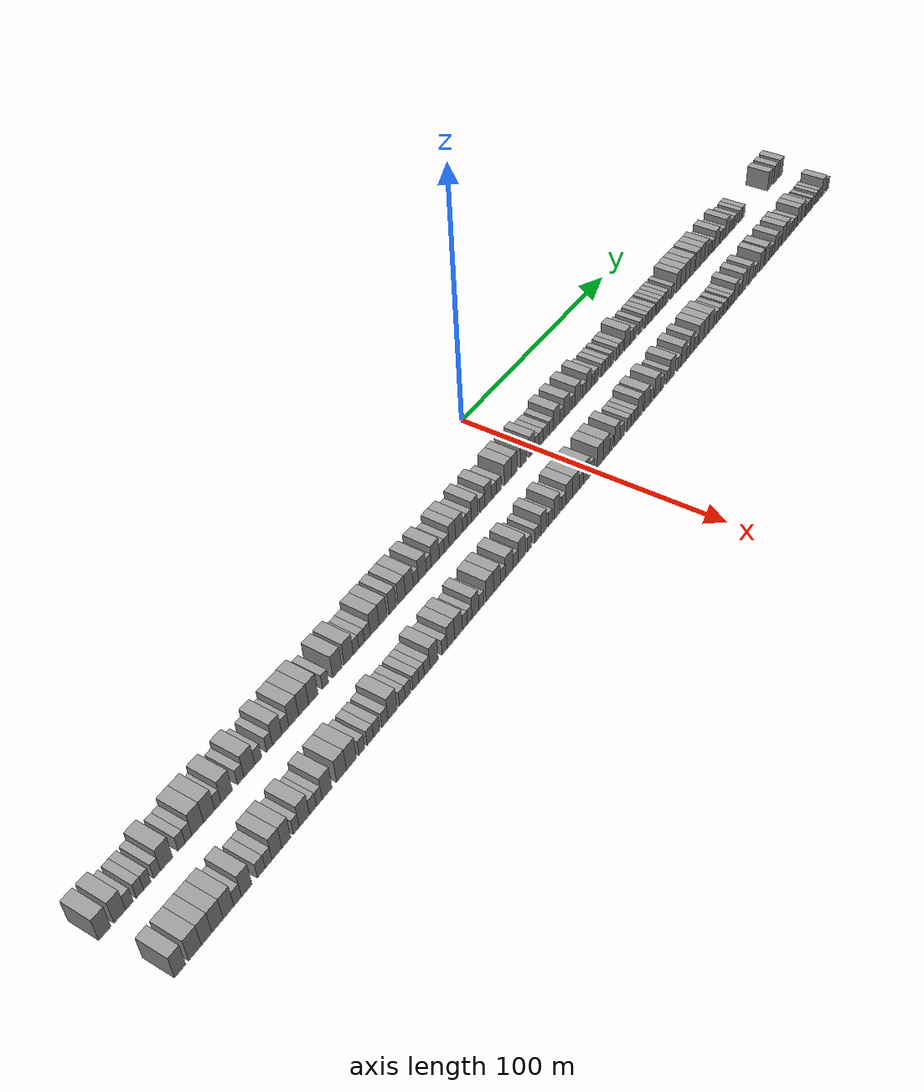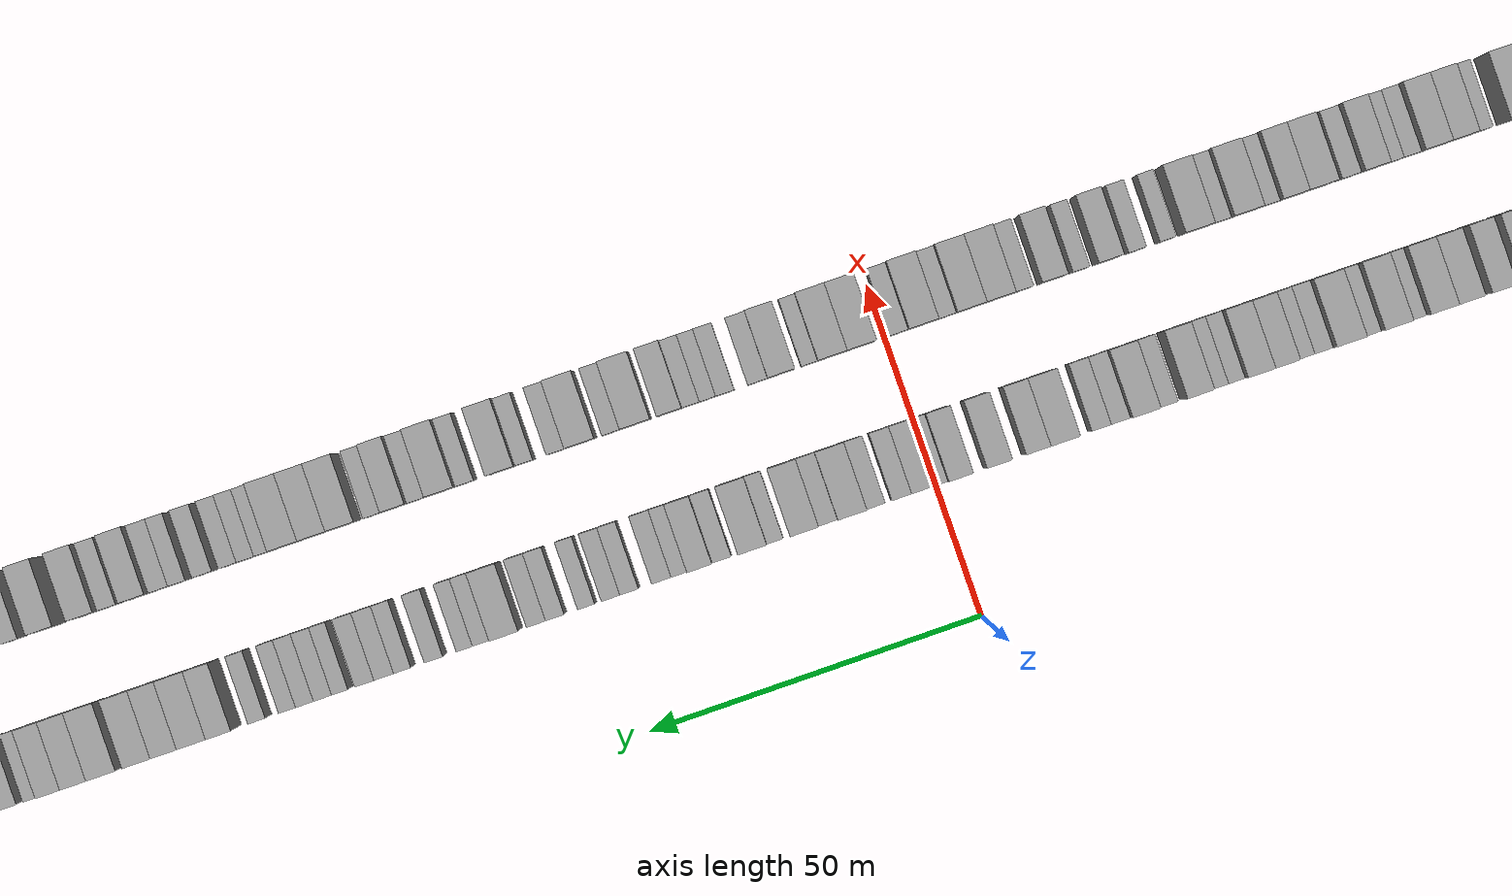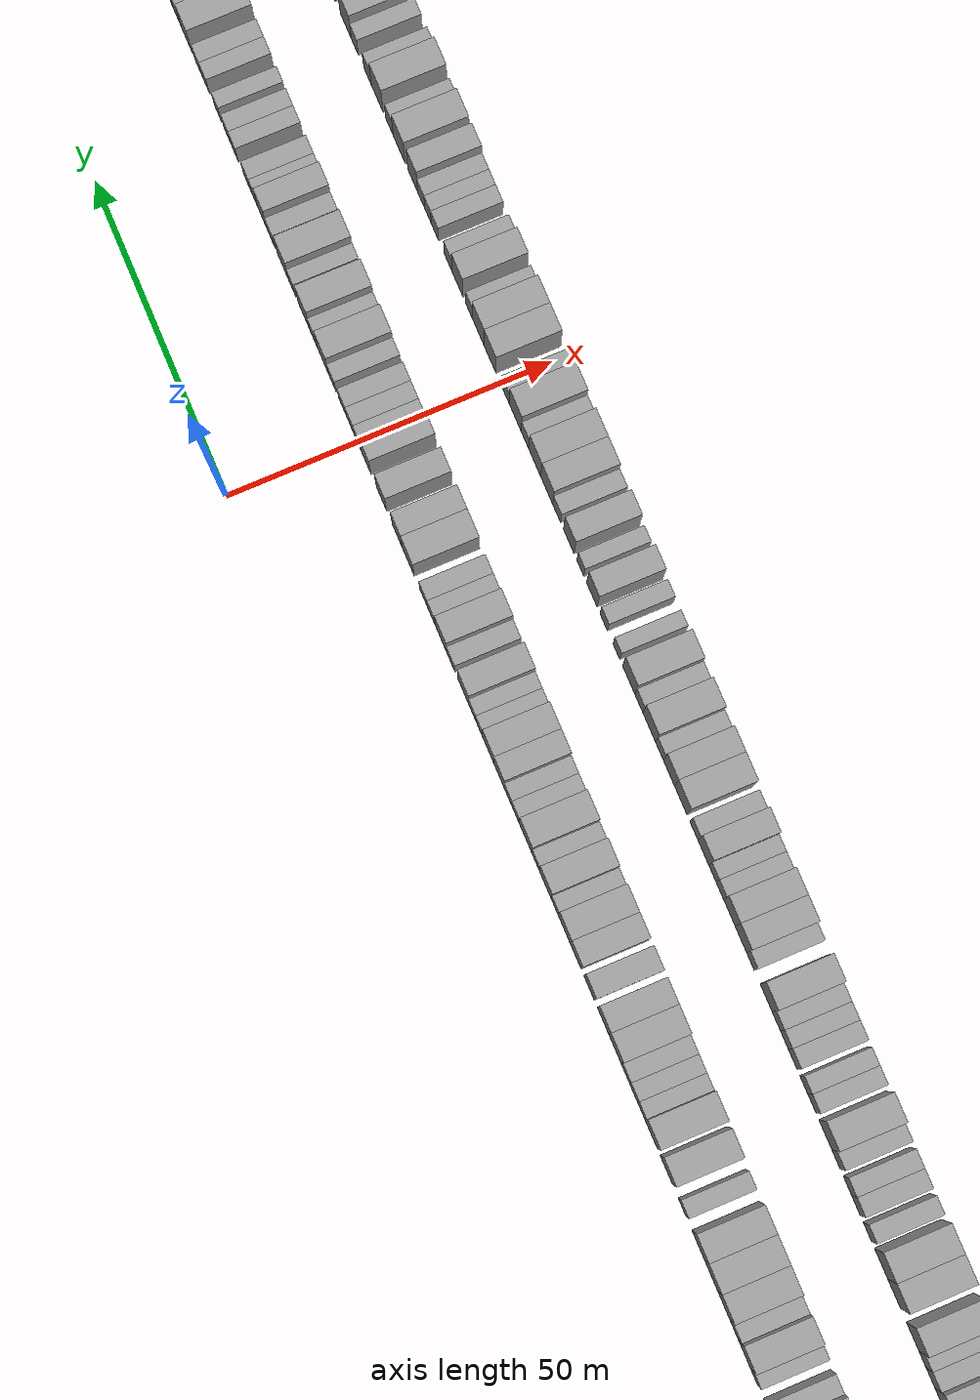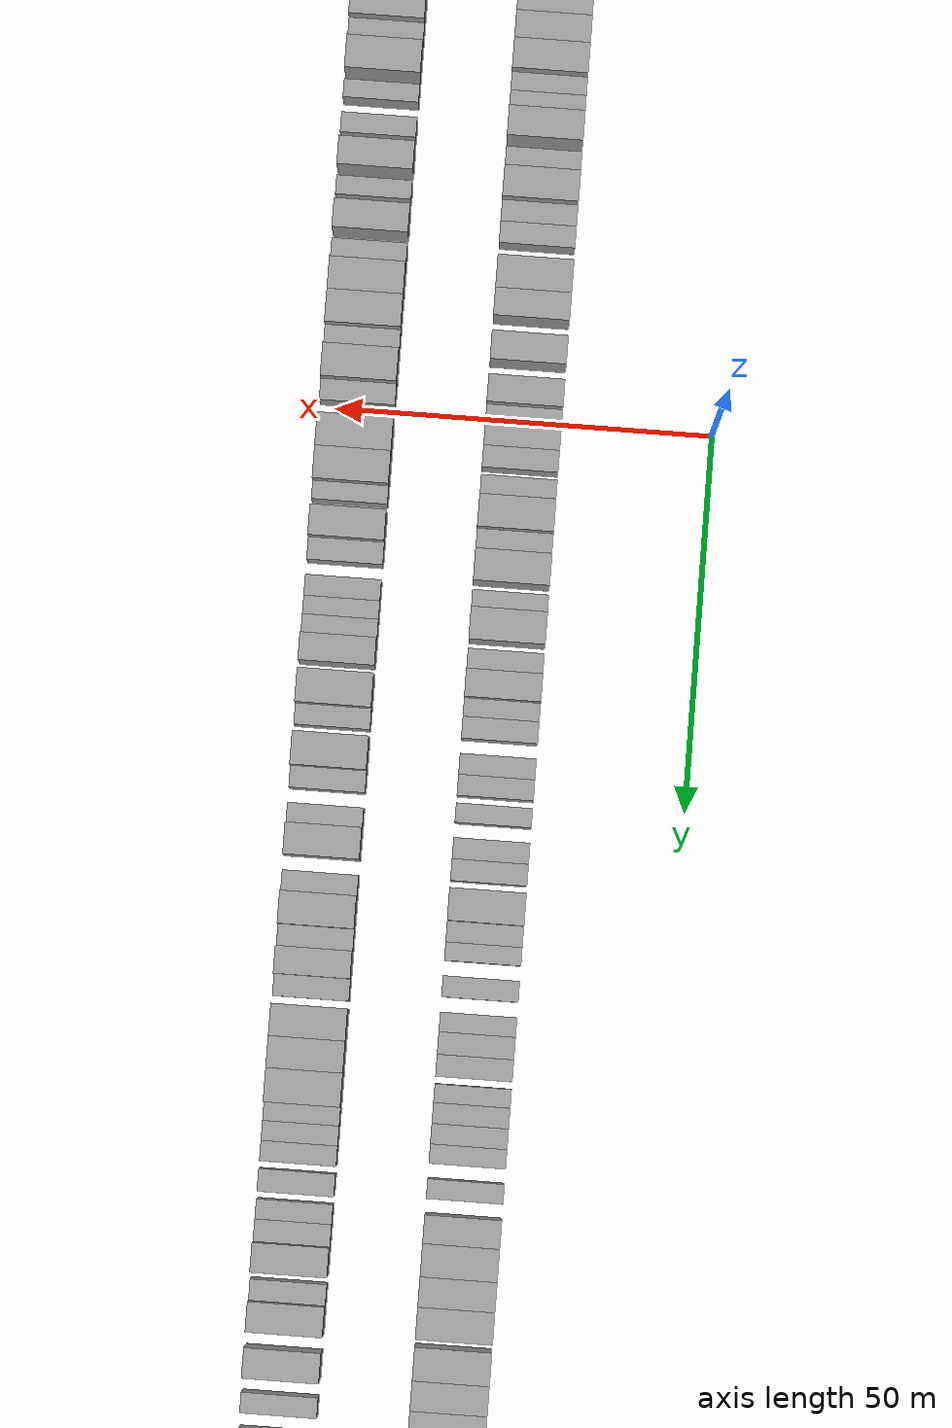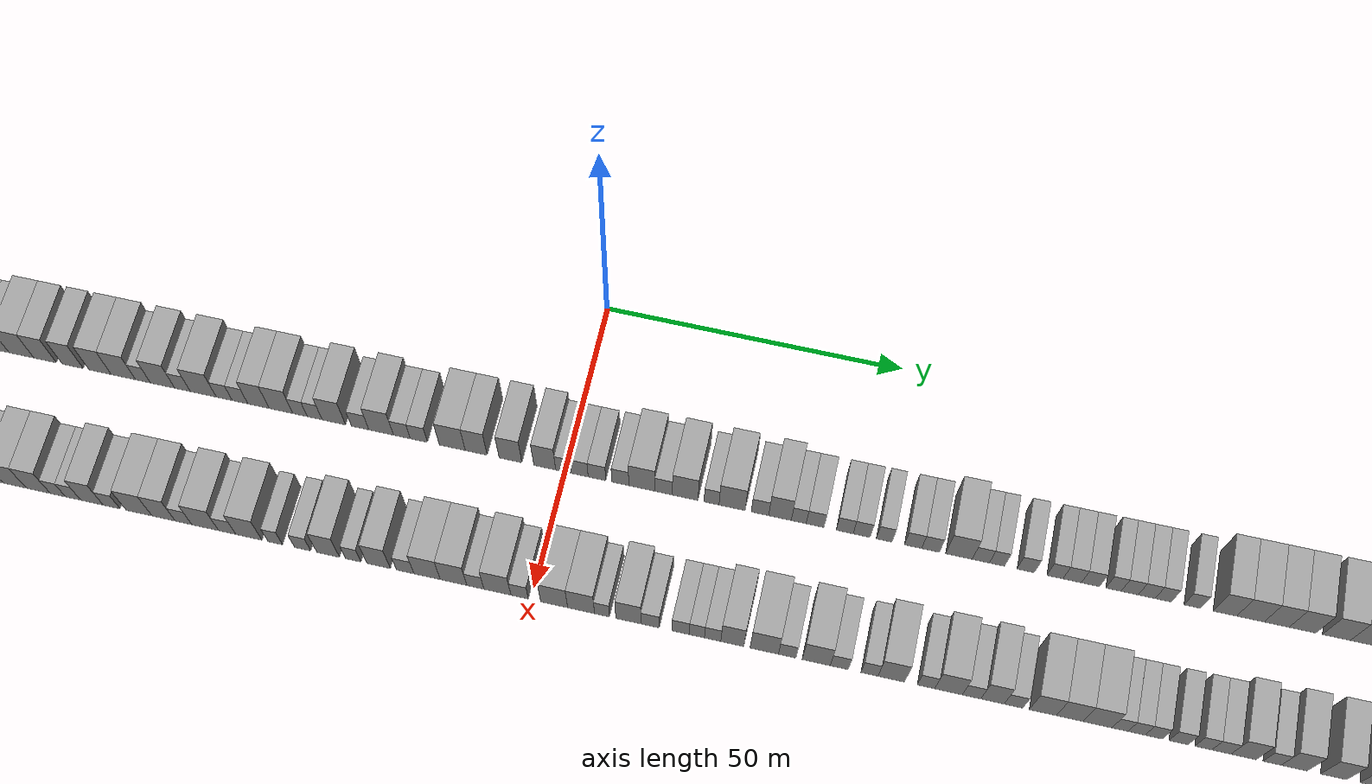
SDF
<sdf version="1.6">
 <world name="default">
  <scene>
   <sky><clouds><speed>12</speed></clouds></sky>
   <ambient>0.4 0.4 0.4 1</ambient>
   <background>0.7 0.7 0.7 1</background>
   <shadows>1</shadows>
  </scene>
  <gravity>0 0 -9.8066</gravity>
  <magnetic_field>6e-06 2.3e-05 -4.2e-05</magnetic_field>
  <physics default="0" name="default_physics" type="ode">
   <ode>
    <solver>
     <type>quick</type>
     <iters>10</iters>
     <sor>1.0</sor>
     <use_dynamic_moi_rescaling>0</use_dynamic_moi_rescaling>
    </solver>
    <constraints>
     <cfm>0</cfm>
     <erp>0.2</erp>
     <contact_max_correcting_vel>100</contact_max_correcting_vel>
     <contact_surface_layer>0.001</contact_surface_layer>
    </constraints>
   </ode>
   <max_step_size>0.004</max_step_size>
   <real_time_factor>1</real_time_factor>
   <real_time_update_rate>250</real_time_update_rate>
  </physics>
  <light name="sun" type="directional">
   <pose>0 0 10 0 0 0</pose>
   <diffuse>0.8 0.8 0.8 1</diffuse>
   <specular>0.2 0.2 0.2 1</specular>
   <attenuation>
    <range>1000</range>
    <constant>0.9</constant>
    <linear>0.01</linear>
    <quadratic>0.001</quadratic>
   </attenuation>
   <direction>-0.5 0.1 -0.9</direction>
  </light>
  <model name="building_1">
   <static>1</static>
   <pose>25.0000 -201.9486 0 0.000000 0.000000 0.000000</pose>
   <link name="link">
    <pose>0 0 4.50 0 0 0</pose>
    <collision name="collision"><geometry><box><size>10.0000 4.1028 9.0000</size></box></geometry></collision>
    <visual name="visual">
     <cast_shadows>0</cast_shadows>
     <geometry><box><size>10.0000 4.1028 9.0000</size></box></geometry>
     <material>
      <script>
       <uri>model://grey_wall/materials/scripts</uri>
       <uri>model://grey_wall/materials/textures</uri>
       <name>vrc/grey_wall</name>
      </script>
     </material>
    </visual>
   </link>
  </model>
  <model name="building_2">
   <static>1</static>
   <pose>25.0000 -196.9260 0 0.000000 0.000000 0.000000</pose>
   <link name="link">
    <pose>0 0 4.50 0 0 0</pose>
    <collision name="collision"><geometry><box><size>10.0000 3.9423 9.0000</size></box></geometry></collision>
    <visual name="visual">
     <cast_shadows>0</cast_shadows>
     <geometry><box><size>10.0000 3.9423 9.0000</size></box></geometry>
     <material>
      <script>
       <uri>model://grey_wall/materials/scripts</uri>
       <uri>model://grey_wall/materials/textures</uri>
       <name>vrc/grey_wall</name>
      </script>
     </material>
    </visual>
   </link>
  </model>
  <model name="building_3">
   <static>1</static>
   <pose>25.0000 -193.6295 0 0.000000 0.000000 0.000000</pose>
   <link name="link">
    <pose>0 0 3.00 0 0 0</pose>
    <collision name="collision"><geometry><box><size>10.0000 2.6506 6.0000</size></box></geometry></collision>
    <visual name="visual">
     <cast_shadows>0</cast_shadows>
     <geometry><box><size>10.0000 2.6506 6.0000</size></box></geometry>
     <material>
      <script>
       <uri>model://grey_wall/materials/scripts</uri>
       <uri>model://grey_wall/materials/textures</uri>
       <name>vrc/grey_wall</name>
      </script>
     </material>
    </visual>
   </link>
  </model>
  <model name="building_4">
   <static>1</static>
   <pose>25.0000 -190.0197 0 0.000000 0.000000 0.000000</pose>
   <link name="link">
    <pose>0 0 3.00 0 0 0</pose>
    <collision name="collision"><geometry><box><size>10.0000 2.5690 6.0000</size></box></geometry></collision>
    <visual name="visual">
     <cast_shadows>0</cast_shadows>
     <geometry><box><size>10.0000 2.5690 6.0000</size></box></geometry>
     <material>
      <script>
       <uri>model://grey_wall/materials/scripts</uri>
       <uri>model://grey_wall/materials/textures</uri>
       <name>vrc/grey_wall</name>
      </script>
     </material>
    </visual>
   </link>
  </model>
  <model name="building_5">
   <static>1</static>
   <pose>25.0000 -187.4292 0 0.000000 0.000000 0.000000</pose>
   <link name="link">
    <pose>0 0 3.00 0 0 0</pose>
    <collision name="collision"><geometry><box><size>10.0000 2.6120 6.0000</size></box></geometry></collision>
    <visual name="visual">
     <cast_shadows>0</cast_shadows>
     <geometry><box><size>10.0000 2.6120 6.0000</size></box></geometry>
     <material>
      <script>
       <uri>model://grey_wall/materials/scripts</uri>
       <uri>model://grey_wall/materials/textures</uri>
       <name>vrc/grey_wall</name>
      </script>
     </material>
    </visual>
   </link>
  </model>
  <model name="building_6">
   <static>1</static>
   <pose>25.0000 -183.9190 0 0.000000 0.000000 0.000000</pose>
   <link name="link">
    <pose>0 0 3.00 0 0 0</pose>
    <collision name="collision"><geometry><box><size>10.0000 2.4084 6.0000</size></box></geometry></collision>
    <visual name="visual">
     <cast_shadows>0</cast_shadows>
     <geometry><box><size>10.0000 2.4084 6.0000</size></box></geometry>
     <material>
      <script>
       <uri>model://grey_wall/materials/scripts</uri>
       <uri>model://grey_wall/materials/textures</uri>
       <name>vrc/grey_wall</name>
      </script>
     </material>
    </visual>
   </link>
  </model>
  <model name="building_7">
   <static>1</static>
   <pose>25.0000 -180.5216 0 0.000000 0.000000 0.000000</pose>
   <link name="link">
    <pose>0 0 4.50 0 0 0</pose>
    <collision name="collision"><geometry><box><size>10.0000 4.3864 9.0000</size></box></geometry></collision>
    <visual name="visual">
     <cast_shadows>0</cast_shadows>
     <geometry><box><size>10.0000 4.3864 9.0000</size></box></geometry>
     <material>
      <script>
       <uri>model://grey_wall/materials/scripts</uri>
       <uri>model://grey_wall/materials/textures</uri>
       <name>vrc/grey_wall</name>
      </script>
     </material>
    </visual>
   </link>
  </model>
  <model name="building_8">
   <static>1</static>
   <pose>25.0000 -175.0357 0 0.000000 0.000000 0.000000</pose>
   <link name="link">
    <pose>0 0 3.00 0 0 0</pose>
    <collision name="collision"><geometry><box><size>10.0000 2.5853 6.0000</size></box></geometry></collision>
    <visual name="visual">
     <cast_shadows>0</cast_shadows>
     <geometry><box><size>10.0000 2.5853 6.0000</size></box></geometry>
     <material>
      <script>
       <uri>model://grey_wall/materials/scripts</uri>
       <uri>model://grey_wall/materials/textures</uri>
       <name>vrc/grey_wall</name>
      </script>
     </material>
    </visual>
   </link>
  </model>
  <model name="building_9">
   <static>1</static>
   <pose>25.0000 -172.4799 0 0.000000 0.000000 0.000000</pose>
   <link name="link">
    <pose>0 0 3.00 0 0 0</pose>
    <collision name="collision"><geometry><box><size>10.0000 2.5263 6.0000</size></box></geometry></collision>
    <visual name="visual">
     <cast_shadows>0</cast_shadows>
     <geometry><box><size>10.0000 2.5263 6.0000</size></box></geometry>
     <material>
      <script>
       <uri>model://grey_wall/materials/scripts</uri>
       <uri>model://grey_wall/materials/textures</uri>
       <name>vrc/grey_wall</name>
      </script>
     </material>
    </visual>
   </link>
  </model>
  <model name="building_10">
   <static>1</static>
   <pose>25.0000 -169.0227 0 0.000000 0.000000 0.000000</pose>
   <link name="link">
    <pose>0 0 4.50 0 0 0</pose>
    <collision name="collision"><geometry><box><size>10.0000 4.3881 9.0000</size></box></geometry></collision>
    <visual name="visual">
     <cast_shadows>0</cast_shadows>
     <geometry><box><size>10.0000 4.3881 9.0000</size></box></geometry>
     <material>
      <script>
       <uri>model://grey_wall/materials/scripts</uri>
       <uri>model://grey_wall/materials/textures</uri>
       <name>vrc/grey_wall</name>
      </script>
     </material>
    </visual>
   </link>
  </model>
  <model name="building_11">
   <static>1</static>
   <pose>25.0000 -164.6957 0 0.000000 0.000000 0.000000</pose>
   <link name="link">
    <pose>0 0 4.50 0 0 0</pose>
    <collision name="collision"><geometry><box><size>10.0000 4.2658 9.0000</size></box></geometry></collision>
    <visual name="visual">
     <cast_shadows>0</cast_shadows>
     <geometry><box><size>10.0000 4.2658 9.0000</size></box></geometry>
     <material>
      <script>
       <uri>model://grey_wall/materials/scripts</uri>
       <uri>model://grey_wall/materials/textures</uri>
       <name>vrc/grey_wall</name>
      </script>
     </material>
    </visual>
   </link>
  </model>
  <model name="building_12">
   <static>1</static>
   <pose>25.0000 -161.3127 0 0.000000 0.000000 0.000000</pose>
   <link name="link">
    <pose>0 0 3.00 0 0 0</pose>
    <collision name="collision"><geometry><box><size>10.0000 2.5003 6.0000</size></box></geometry></collision>
    <visual name="visual">
     <cast_shadows>0</cast_shadows>
     <geometry><box><size>10.0000 2.5003 6.0000</size></box></geometry>
     <material>
      <script>
       <uri>model://grey_wall/materials/scripts</uri>
       <uri>model://grey_wall/materials/textures</uri>
       <name>vrc/grey_wall</name>
      </script>
     </material>
    </visual>
   </link>
  </model>
  <model name="building_13">
   <static>1</static>
   <pose>25.0000 -157.8440 0 0.000000 0.000000 0.000000</pose>
   <link name="link">
    <pose>0 0 4.50 0 0 0</pose>
    <collision name="collision"><geometry><box><size>10.0000 4.4371 9.0000</size></box></geometry></collision>
    <visual name="visual">
     <cast_shadows>0</cast_shadows>
     <geometry><box><size>10.0000 4.4371 9.0000</size></box></geometry>
     <material>
      <script>
       <uri>model://grey_wall/materials/scripts</uri>
       <uri>model://grey_wall/materials/textures</uri>
       <name>vrc/grey_wall</name>
      </script>
     </material>
    </visual>
   </link>
  </model>
  <model name="building_14">
   <static>1</static>
   <pose>25.0000 -152.3269 0 0.000000 0.000000 0.000000</pose>
   <link name="link">
    <pose>0 0 3.00 0 0 0</pose>
    <collision name="collision"><geometry><box><size>10.0000 2.5972 6.0000</size></box></geometry></collision>
    <visual name="visual">
     <cast_shadows>0</cast_shadows>
     <geometry><box><size>10.0000 2.5972 6.0000</size></box></geometry>
     <material>
      <script>
       <uri>model://grey_wall/materials/scripts</uri>
       <uri>model://grey_wall/materials/textures</uri>
       <name>vrc/grey_wall</name>
      </script>
     </material>
    </visual>
   </link>
  </model>
  <model name="building_15">
   <static>1</static>
   <pose>25.0000 -148.8110 0 0.000000 0.000000 0.000000</pose>
   <link name="link">
    <pose>0 0 4.50 0 0 0</pose>
    <collision name="collision"><geometry><box><size>10.0000 4.4345 9.0000</size></box></geometry></collision>
    <visual name="visual">
     <cast_shadows>0</cast_shadows>
     <geometry><box><size>10.0000 4.4345 9.0000</size></box></geometry>
     <material>
      <script>
       <uri>model://grey_wall/materials/scripts</uri>
       <uri>model://grey_wall/materials/textures</uri>
       <name>vrc/grey_wall</name>
      </script>
     </material>
    </visual>
   </link>
  </model>
  <model name="building_16">
   <static>1</static>
   <pose>25.0000 -145.1542 0 0.000000 0.000000 0.000000</pose>
   <link name="link">
    <pose>0 0 3.00 0 0 0</pose>
    <collision name="collision"><geometry><box><size>10.0000 2.8792 6.0000</size></box></geometry></collision>
    <visual name="visual">
     <cast_shadows>0</cast_shadows>
     <geometry><box><size>10.0000 2.8792 6.0000</size></box></geometry>
     <material>
      <script>
       <uri>model://grey_wall/materials/scripts</uri>
       <uri>model://grey_wall/materials/textures</uri>
       <name>vrc/grey_wall</name>
      </script>
     </material>
    </visual>
   </link>
  </model>
  <model name="building_17">
   <static>1</static>
   <pose>25.0000 -140.5001 0 0.000000 0.000000 0.000000</pose>
   <link name="link">
    <pose>0 0 3.00 0 0 0</pose>
    <collision name="collision"><geometry><box><size>10.0000 2.4290 6.0000</size></box></geometry></collision>
    <visual name="visual">
     <cast_shadows>0</cast_shadows>
     <geometry><box><size>10.0000 2.4290 6.0000</size></box></geometry>
     <material>
      <script>
       <uri>model://grey_wall/materials/scripts</uri>
       <uri>model://grey_wall/materials/textures</uri>
       <name>vrc/grey_wall</name>
      </script>
     </material>
    </visual>
   </link>
  </model>
  <model name="building_18">
   <static>1</static>
   <pose>25.0000 -137.2405 0 0.000000 0.000000 0.000000</pose>
   <link name="link">
    <pose>0 0 4.50 0 0 0</pose>
    <collision name="collision"><geometry><box><size>10.0000 4.0901 9.0000</size></box></geometry></collision>
    <visual name="visual">
     <cast_shadows>0</cast_shadows>
     <geometry><box><size>10.0000 4.0901 9.0000</size></box></geometry>
     <material>
      <script>
       <uri>model://grey_wall/materials/scripts</uri>
       <uri>model://grey_wall/materials/textures</uri>
       <name>vrc/grey_wall</name>
      </script>
     </material>
    </visual>
   </link>
  </model>
  <model name="building_19">
   <static>1</static>
   <pose>25.0000 -133.7111 0 0.000000 0.000000 0.000000</pose>
   <link name="link">
    <pose>0 0 3.00 0 0 0</pose>
    <collision name="collision"><geometry><box><size>10.0000 2.9687 6.0000</size></box></geometry></collision>
    <visual name="visual">
     <cast_shadows>0</cast_shadows>
     <geometry><box><size>10.0000 2.9687 6.0000</size></box></geometry>
     <material>
      <script>
       <uri>model://grey_wall/materials/scripts</uri>
       <uri>model://grey_wall/materials/textures</uri>
       <name>vrc/grey_wall</name>
      </script>
     </material>
    </visual>
   </link>
  </model>
  <model name="building_20">
   <static>1</static>
   <pose>25.0000 -130.1012 0 0.000000 0.000000 0.000000</pose>
   <link name="link">
    <pose>0 0 4.50 0 0 0</pose>
    <collision name="collision"><geometry><box><size>10.0000 4.2512 9.0000</size></box></geometry></collision>
    <visual name="visual">
     <cast_shadows>0</cast_shadows>
     <geometry><box><size>10.0000 4.2512 9.0000</size></box></geometry>
     <material>
      <script>
       <uri>model://grey_wall/materials/scripts</uri>
       <uri>model://grey_wall/materials/textures</uri>
       <name>vrc/grey_wall</name>
      </script>
     </material>
    </visual>
   </link>
  </model>
  <model name="building_21">
   <static>1</static>
   <pose>25.0000 -125.7690 0 0.000000 0.000000 0.000000</pose>
   <link name="link">
    <pose>0 0 4.50 0 0 0</pose>
    <collision name="collision"><geometry><box><size>10.0000 4.4133 9.0000</size></box></geometry></collision>
    <visual name="visual">
     <cast_shadows>0</cast_shadows>
     <geometry><box><size>10.0000 4.4133 9.0000</size></box></geometry>
     <material>
      <script>
       <uri>model://grey_wall/materials/scripts</uri>
       <uri>model://grey_wall/materials/textures</uri>
       <name>vrc/grey_wall</name>
      </script>
     </material>
    </visual>
   </link>
  </model>
  <model name="building_22">
   <static>1</static>
   <pose>25.0000 -121.4568 0 0.000000 0.000000 0.000000</pose>
   <link name="link">
    <pose>0 0 4.50 0 0 0</pose>
    <collision name="collision"><geometry><box><size>10.0000 4.2110 9.0000</size></box></geometry></collision>
    <visual name="visual">
     <cast_shadows>0</cast_shadows>
     <geometry><box><size>10.0000 4.2110 9.0000</size></box></geometry>
     <material>
      <script>
       <uri>model://grey_wall/materials/scripts</uri>
       <uri>model://grey_wall/materials/textures</uri>
       <name>vrc/grey_wall</name>
      </script>
     </material>
    </visual>
   </link>
  </model>
  <model name="building_23">
   <static>1</static>
   <pose>25.0000 -115.9978 0 0.000000 0.000000 0.000000</pose>
   <link name="link">
    <pose>0 0 3.00 0 0 0</pose>
    <collision name="collision"><geometry><box><size>10.0000 2.7069 6.0000</size></box></geometry></collision>
    <visual name="visual">
     <cast_shadows>0</cast_shadows>
     <geometry><box><size>10.0000 2.7069 6.0000</size></box></geometry>
     <material>
      <script>
       <uri>model://grey_wall/materials/scripts</uri>
       <uri>model://grey_wall/materials/textures</uri>
       <name>vrc/grey_wall</name>
      </script>
     </material>
    </visual>
   </link>
  </model>
  <model name="building_24">
   <static>1</static>
   <pose>25.0000 -110.5085 0 0.000000 0.000000 0.000000</pose>
   <link name="link">
    <pose>0 0 4.50 0 0 0</pose>
    <collision name="collision"><geometry><box><size>10.0000 4.2718 9.0000</size></box></geometry></collision>
    <visual name="visual">
     <cast_shadows>0</cast_shadows>
     <geometry><box><size>10.0000 4.2718 9.0000</size></box></geometry>
     <material>
      <script>
       <uri>model://grey_wall/materials/scripts</uri>
       <uri>model://grey_wall/materials/textures</uri>
       <name>vrc/grey_wall</name>
      </script>
     </material>
    </visual>
   </link>
  </model>
  <model name="building_25">
   <static>1</static>
   <pose>25.0000 -105.1688 0 0.000000 0.000000 0.000000</pose>
   <link name="link">
    <pose>0 0 4.50 0 0 0</pose>
    <collision name="collision"><geometry><box><size>10.0000 4.4077 9.0000</size></box></geometry></collision>
    <visual name="visual">
     <cast_shadows>0</cast_shadows>
     <geometry><box><size>10.0000 4.4077 9.0000</size></box></geometry>
     <material>
      <script>
       <uri>model://grey_wall/materials/scripts</uri>
       <uri>model://grey_wall/materials/textures</uri>
       <name>vrc/grey_wall</name>
      </script>
     </material>
    </visual>
   </link>
  </model>
  <model name="building_26">
   <static>1</static>
   <pose>25.0000 -101.6888 0 0.000000 0.000000 0.000000</pose>
   <link name="link">
    <pose>0 0 3.00 0 0 0</pose>
    <collision name="collision"><geometry><box><size>10.0000 2.5521 6.0000</size></box></geometry></collision>
    <visual name="visual">
     <cast_shadows>0</cast_shadows>
     <geometry><box><size>10.0000 2.5521 6.0000</size></box></geometry>
     <material>
      <script>
       <uri>model://grey_wall/materials/scripts</uri>
       <uri>model://grey_wall/materials/textures</uri>
       <name>vrc/grey_wall</name>
      </script>
     </material>
    </visual>
   </link>
  </model>
  <model name="building_27">
   <static>1</static>
   <pose>25.0000 -99.0381 0 0.000000 0.000000 0.000000</pose>
   <link name="link">
    <pose>0 0 3.00 0 0 0</pose>
    <collision name="collision"><geometry><box><size>10.0000 2.7493 6.0000</size></box></geometry></collision>
    <visual name="visual">
     <cast_shadows>0</cast_shadows>
     <geometry><box><size>10.0000 2.7493 6.0000</size></box></geometry>
     <material>
      <script>
       <uri>model://grey_wall/materials/scripts</uri>
       <uri>model://grey_wall/materials/textures</uri>
       <name>vrc/grey_wall</name>
      </script>
     </material>
    </visual>
   </link>
  </model>
  <model name="building_28">
   <static>1</static>
   <pose>25.0000 -96.2116 0 0.000000 0.000000 0.000000</pose>
   <link name="link">
    <pose>0 0 3.00 0 0 0</pose>
    <collision name="collision"><geometry><box><size>10.0000 2.9036 6.0000</size></box></geometry></collision>
    <visual name="visual">
     <cast_shadows>0</cast_shadows>
     <geometry><box><size>10.0000 2.9036 6.0000</size></box></geometry>
     <material>
      <script>
       <uri>model://grey_wall/materials/scripts</uri>
       <uri>model://grey_wall/materials/textures</uri>
       <name>vrc/grey_wall</name>
      </script>
     </material>
    </visual>
   </link>
  </model>
  <model name="building_29">
   <static>1</static>
   <pose>25.0000 -92.5882 0 0.000000 0.000000 0.000000</pose>
   <link name="link">
    <pose>0 0 4.50 0 0 0</pose>
    <collision name="collision"><geometry><box><size>10.0000 4.3431 9.0000</size></box></geometry></collision>
    <visual name="visual">
     <cast_shadows>0</cast_shadows>
     <geometry><box><size>10.0000 4.3431 9.0000</size></box></geometry>
     <material>
      <script>
       <uri>model://grey_wall/materials/scripts</uri>
       <uri>model://grey_wall/materials/textures</uri>
       <name>vrc/grey_wall</name>
      </script>
     </material>
    </visual>
   </link>
  </model>
  <model name="building_30">
   <static>1</static>
   <pose>25.0000 -88.4454 0 0.000000 0.000000 0.000000</pose>
   <link name="link">
    <pose>0 0 4.50 0 0 0</pose>
    <collision name="collision"><geometry><box><size>10.0000 3.9424 9.0000</size></box></geometry></collision>
    <visual name="visual">
     <cast_shadows>0</cast_shadows>
     <geometry><box><size>10.0000 3.9424 9.0000</size></box></geometry>
     <material>
      <script>
       <uri>model://grey_wall/materials/scripts</uri>
       <uri>model://grey_wall/materials/textures</uri>
       <name>vrc/grey_wall</name>
      </script>
     </material>
    </visual>
   </link>
  </model>
  <model name="building_31">
   <static>1</static>
   <pose>25.0000 -83.6475 0 0.000000 0.000000 0.000000</pose>
   <link name="link">
    <pose>0 0 4.50 0 0 0</pose>
    <collision name="collision"><geometry><box><size>10.0000 3.6534 9.0000</size></box></geometry></collision>
    <visual name="visual">
     <cast_shadows>0</cast_shadows>
     <geometry><box><size>10.0000 3.6534 9.0000</size></box></geometry>
     <material>
      <script>
       <uri>model://grey_wall/materials/scripts</uri>
       <uri>model://grey_wall/materials/textures</uri>
       <name>vrc/grey_wall</name>
      </script>
     </material>
    </visual>
   </link>
  </model>
  <model name="building_32">
   <static>1</static>
   <pose>25.0000 -78.8852 0 0.000000 0.000000 0.000000</pose>
   <link name="link">
    <pose>0 0 4.50 0 0 0</pose>
    <collision name="collision"><geometry><box><size>10.0000 3.8712 9.0000</size></box></geometry></collision>
    <visual name="visual">
     <cast_shadows>0</cast_shadows>
     <geometry><box><size>10.0000 3.8712 9.0000</size></box></geometry>
     <material>
      <script>
       <uri>model://grey_wall/materials/scripts</uri>
       <uri>model://grey_wall/materials/textures</uri>
       <name>vrc/grey_wall</name>
      </script>
     </material>
    </visual>
   </link>
  </model>
  <model name="building_33">
   <static>1</static>
   <pose>25.0000 -74.8442 0 0.000000 0.000000 0.000000</pose>
   <link name="link">
    <pose>0 0 4.50 0 0 0</pose>
    <collision name="collision"><geometry><box><size>10.0000 4.2107 9.0000</size></box></geometry></collision>
    <visual name="visual">
     <cast_shadows>0</cast_shadows>
     <geometry><box><size>10.0000 4.2107 9.0000</size></box></geometry>
     <material>
      <script>
       <uri>model://grey_wall/materials/scripts</uri>
       <uri>model://grey_wall/materials/textures</uri>
       <name>vrc/grey_wall</name>
      </script>
     </material>
    </visual>
   </link>
  </model>
  <model name="building_34">
   <static>1</static>
   <pose>25.0000 -71.4549 0 0.000000 0.000000 0.000000</pose>
   <link name="link">
    <pose>0 0 3.00 0 0 0</pose>
    <collision name="collision"><geometry><box><size>10.0000 2.5680 6.0000</size></box></geometry></collision>
    <visual name="visual">
     <cast_shadows>0</cast_shadows>
     <geometry><box><size>10.0000 2.5680 6.0000</size></box></geometry>
     <material>
      <script>
       <uri>model://grey_wall/materials/scripts</uri>
       <uri>model://grey_wall/materials/textures</uri>
       <name>vrc/grey_wall</name>
      </script>
     </material>
    </visual>
   </link>
  </model>
  <model name="building_35">
   <static>1</static>
   <pose>25.0000 -68.0757 0 0.000000 0.000000 0.000000</pose>
   <link name="link">
    <pose>0 0 4.50 0 0 0</pose>
    <collision name="collision"><geometry><box><size>10.0000 4.1905 9.0000</size></box></geometry></collision>
    <visual name="visual">
     <cast_shadows>0</cast_shadows>
     <geometry><box><size>10.0000 4.1905 9.0000</size></box></geometry>
     <material>
      <script>
       <uri>model://grey_wall/materials/scripts</uri>
       <uri>model://grey_wall/materials/textures</uri>
       <name>vrc/grey_wall</name>
      </script>
     </material>
    </visual>
   </link>
  </model>
  <model name="building_36">
   <static>1</static>
   <pose>25.0000 -64.6433 0 0.000000 0.000000 0.000000</pose>
   <link name="link">
    <pose>0 0 3.00 0 0 0</pose>
    <collision name="collision"><geometry><box><size>10.0000 2.6743 6.0000</size></box></geometry></collision>
    <visual name="visual">
     <cast_shadows>0</cast_shadows>
     <geometry><box><size>10.0000 2.6743 6.0000</size></box></geometry>
     <material>
      <script>
       <uri>model://grey_wall/materials/scripts</uri>
       <uri>model://grey_wall/materials/textures</uri>
       <name>vrc/grey_wall</name>
      </script>
     </material>
    </visual>
   </link>
  </model>
  <model name="building_37">
   <static>1</static>
   <pose>25.0000 -61.0658 0 0.000000 0.000000 0.000000</pose>
   <link name="link">
    <pose>0 0 4.50 0 0 0</pose>
    <collision name="collision"><geometry><box><size>10.0000 4.4806 9.0000</size></box></geometry></collision>
    <visual name="visual">
     <cast_shadows>0</cast_shadows>
     <geometry><box><size>10.0000 4.4806 9.0000</size></box></geometry>
     <material>
      <script>
       <uri>model://grey_wall/materials/scripts</uri>
       <uri>model://grey_wall/materials/textures</uri>
       <name>vrc/grey_wall</name>
      </script>
     </material>
    </visual>
   </link>
  </model>
  <model name="building_38">
   <static>1</static>
   <pose>25.0000 -57.4622 0 0.000000 0.000000 0.000000</pose>
   <link name="link">
    <pose>0 0 3.00 0 0 0</pose>
    <collision name="collision"><geometry><box><size>10.0000 2.7266 6.0000</size></box></geometry></collision>
    <visual name="visual">
     <cast_shadows>0</cast_shadows>
     <geometry><box><size>10.0000 2.7266 6.0000</size></box></geometry>
     <material>
      <script>
       <uri>model://grey_wall/materials/scripts</uri>
       <uri>model://grey_wall/materials/textures</uri>
       <name>vrc/grey_wall</name>
      </script>
     </material>
    </visual>
   </link>
  </model>
  <model name="building_39">
   <static>1</static>
   <pose>25.0000 -54.7603 0 0.000000 0.000000 0.000000</pose>
   <link name="link">
    <pose>0 0 3.00 0 0 0</pose>
    <collision name="collision"><geometry><box><size>10.0000 2.6773 6.0000</size></box></geometry></collision>
    <visual name="visual">
     <cast_shadows>0</cast_shadows>
     <geometry><box><size>10.0000 2.6773 6.0000</size></box></geometry>
     <material>
      <script>
       <uri>model://grey_wall/materials/scripts</uri>
       <uri>model://grey_wall/materials/textures</uri>
       <name>vrc/grey_wall</name>
      </script>
     </material>
    </visual>
   </link>
  </model>
  <model name="building_40">
   <static>1</static>
   <pose>25.0000 -51.5983 0 0.000000 0.000000 0.000000</pose>
   <link name="link">
    <pose>0 0 4.50 0 0 0</pose>
    <collision name="collision"><geometry><box><size>10.0000 3.6467 9.0000</size></box></geometry></collision>
    <visual name="visual">
     <cast_shadows>0</cast_shadows>
     <geometry><box><size>10.0000 3.6467 9.0000</size></box></geometry>
     <material>
      <script>
       <uri>model://grey_wall/materials/scripts</uri>
       <uri>model://grey_wall/materials/textures</uri>
       <name>vrc/grey_wall</name>
      </script>
     </material>
    </visual>
   </link>
  </model>
  <model name="building_41">
   <static>1</static>
   <pose>25.0000 -47.7491 0 0.000000 0.000000 0.000000</pose>
   <link name="link">
    <pose>0 0 4.50 0 0 0</pose>
    <collision name="collision"><geometry><box><size>10.0000 4.0517 9.0000</size></box></geometry></collision>
    <visual name="visual">
     <cast_shadows>0</cast_shadows>
     <geometry><box><size>10.0000 4.0517 9.0000</size></box></geometry>
     <material>
      <script>
       <uri>model://grey_wall/materials/scripts</uri>
       <uri>model://grey_wall/materials/textures</uri>
       <name>vrc/grey_wall</name>
      </script>
     </material>
    </visual>
   </link>
  </model>
  <model name="building_42">
   <static>1</static>
   <pose>25.0000 -44.4981 0 0.000000 0.000000 0.000000</pose>
   <link name="link">
    <pose>0 0 3.00 0 0 0</pose>
    <collision name="collision"><geometry><box><size>10.0000 2.4504 6.0000</size></box></geometry></collision>
    <visual name="visual">
     <cast_shadows>0</cast_shadows>
     <geometry><box><size>10.0000 2.4504 6.0000</size></box></geometry>
     <material>
      <script>
       <uri>model://grey_wall/materials/scripts</uri>
       <uri>model://grey_wall/materials/textures</uri>
       <name>vrc/grey_wall</name>
      </script>
     </material>
    </visual>
   </link>
  </model>
  <model name="building_43">
   <static>1</static>
   <pose>25.0000 -42.0113 0 0.000000 0.000000 0.000000</pose>
   <link name="link">
    <pose>0 0 3.00 0 0 0</pose>
    <collision name="collision"><geometry><box><size>10.0000 2.5232 6.0000</size></box></geometry></collision>
    <visual name="visual">
     <cast_shadows>0</cast_shadows>
     <geometry><box><size>10.0000 2.5232 6.0000</size></box></geometry>
     <material>
      <script>
       <uri>model://grey_wall/materials/scripts</uri>
       <uri>model://grey_wall/materials/textures</uri>
       <name>vrc/grey_wall</name>
      </script>
     </material>
    </visual>
   </link>
  </model>
  <model name="building_44">
   <static>1</static>
   <pose>25.0000 -38.7583 0 0.000000 0.000000 0.000000</pose>
   <link name="link">
    <pose>0 0 4.50 0 0 0</pose>
    <collision name="collision"><geometry><box><size>10.0000 3.9829 9.0000</size></box></geometry></collision>
    <visual name="visual">
     <cast_shadows>0</cast_shadows>
     <geometry><box><size>10.0000 3.9829 9.0000</size></box></geometry>
     <material>
      <script>
       <uri>model://grey_wall/materials/scripts</uri>
       <uri>model://grey_wall/materials/textures</uri>
       <name>vrc/grey_wall</name>
      </script>
     </material>
    </visual>
   </link>
  </model>
  <model name="building_45">
   <static>1</static>
   <pose>25.0000 -34.2935 0 0.000000 0.000000 0.000000</pose>
   <link name="link">
    <pose>0 0 3.00 0 0 0</pose>
    <collision name="collision"><geometry><box><size>10.0000 2.9467 6.0000</size></box></geometry></collision>
    <visual name="visual">
     <cast_shadows>0</cast_shadows>
     <geometry><box><size>10.0000 2.9467 6.0000</size></box></geometry>
     <material>
      <script>
       <uri>model://grey_wall/materials/scripts</uri>
       <uri>model://grey_wall/materials/textures</uri>
       <name>vrc/grey_wall</name>
      </script>
     </material>
    </visual>
   </link>
  </model>
  <model name="building_46">
   <static>1</static>
   <pose>25.0000 -30.7365 0 0.000000 0.000000 0.000000</pose>
   <link name="link">
    <pose>0 0 4.50 0 0 0</pose>
    <collision name="collision"><geometry><box><size>10.0000 4.1672 9.0000</size></box></geometry></collision>
    <visual name="visual">
     <cast_shadows>0</cast_shadows>
     <geometry><box><size>10.0000 4.1672 9.0000</size></box></geometry>
     <material>
      <script>
       <uri>model://grey_wall/materials/scripts</uri>
       <uri>model://grey_wall/materials/textures</uri>
       <name>vrc/grey_wall</name>
      </script>
     </material>
    </visual>
   </link>
  </model>
  <model name="building_47">
   <static>1</static>
   <pose>25.0000 -27.2375 0 0.000000 0.000000 0.000000</pose>
   <link name="link">
    <pose>0 0 3.00 0 0 0</pose>
    <collision name="collision"><geometry><box><size>10.0000 2.8310 6.0000</size></box></geometry></collision>
    <visual name="visual">
     <cast_shadows>0</cast_shadows>
     <geometry><box><size>10.0000 2.8310 6.0000</size></box></geometry>
     <material>
      <script>
       <uri>model://grey_wall/materials/scripts</uri>
       <uri>model://grey_wall/materials/textures</uri>
       <name>vrc/grey_wall</name>
      </script>
     </material>
    </visual>
   </link>
  </model>
  <model name="building_48">
   <static>1</static>
   <pose>25.0000 -24.3723 0 0.000000 0.000000 0.000000</pose>
   <link name="link">
    <pose>0 0 3.00 0 0 0</pose>
    <collision name="collision"><geometry><box><size>10.0000 2.8993 6.0000</size></box></geometry></collision>
    <visual name="visual">
     <cast_shadows>0</cast_shadows>
     <geometry><box><size>10.0000 2.8993 6.0000</size></box></geometry>
     <material>
      <script>
       <uri>model://grey_wall/materials/scripts</uri>
       <uri>model://grey_wall/materials/textures</uri>
       <name>vrc/grey_wall</name>
      </script>
     </material>
    </visual>
   </link>
  </model>
  <model name="building_49">
   <static>1</static>
   <pose>25.0000 -18.7430 0 0.000000 0.000000 0.000000</pose>
   <link name="link">
    <pose>0 0 4.50 0 0 0</pose>
    <collision name="collision"><geometry><box><size>10.0000 4.3593 9.0000</size></box></geometry></collision>
    <visual name="visual">
     <cast_shadows>0</cast_shadows>
     <geometry><box><size>10.0000 4.3593 9.0000</size></box></geometry>
     <material>
      <script>
       <uri>model://grey_wall/materials/scripts</uri>
       <uri>model://grey_wall/materials/textures</uri>
       <name>vrc/grey_wall</name>
      </script>
     </material>
    </visual>
   </link>
  </model>
  <model name="building_50">
   <static>1</static>
   <pose>25.0000 -14.7288 0 0.000000 0.000000 0.000000</pose>
   <link name="link">
    <pose>0 0 4.50 0 0 0</pose>
    <collision name="collision"><geometry><box><size>10.0000 3.6691 9.0000</size></box></geometry></collision>
    <visual name="visual">
     <cast_shadows>0</cast_shadows>
     <geometry><box><size>10.0000 3.6691 9.0000</size></box></geometry>
     <material>
      <script>
       <uri>model://grey_wall/materials/scripts</uri>
       <uri>model://grey_wall/materials/textures</uri>
       <name>vrc/grey_wall</name>
      </script>
     </material>
    </visual>
   </link>
  </model>
  <model name="building_51">
   <static>1</static>
   <pose>25.0000 -8.9990 0 0.000000 0.000000 0.000000</pose>
   <link name="link">
    <pose>0 0 4.50 0 0 0</pose>
    <collision name="collision"><geometry><box><size>10.0000 3.7905 9.0000</size></box></geometry></collision>
    <visual name="visual">
     <cast_shadows>0</cast_shadows>
     <geometry><box><size>10.0000 3.7905 9.0000</size></box></geometry>
     <material>
      <script>
       <uri>model://grey_wall/materials/scripts</uri>
       <uri>model://grey_wall/materials/textures</uri>
       <name>vrc/grey_wall</name>
      </script>
     </material>
    </visual>
   </link>
  </model>
  <model name="building_52">
   <static>1</static>
   <pose>25.0000 -3.2879 0 0.000000 0.000000 0.000000</pose>
   <link name="link">
    <pose>0 0 4.50 0 0 0</pose>
    <collision name="collision"><geometry><box><size>10.0000 3.6317 9.0000</size></box></geometry></collision>
    <visual name="visual">
     <cast_shadows>0</cast_shadows>
     <geometry><box><size>10.0000 3.6317 9.0000</size></box></geometry>
     <material>
      <script>
       <uri>model://grey_wall/materials/scripts</uri>
       <uri>model://grey_wall/materials/textures</uri>
       <name>vrc/grey_wall</name>
      </script>
     </material>
    </visual>
   </link>
  </model>
  <model name="building_53">
   <static>1</static>
   <pose>25.0000 -0.1891 0 0.000000 0.000000 0.000000</pose>
   <link name="link">
    <pose>0 0 3.00 0 0 0</pose>
    <collision name="collision"><geometry><box><size>10.0000 2.5659 6.0000</size></box></geometry></collision>
    <visual name="visual">
     <cast_shadows>0</cast_shadows>
     <geometry><box><size>10.0000 2.5659 6.0000</size></box></geometry>
     <material>
      <script>
       <uri>model://grey_wall/materials/scripts</uri>
       <uri>model://grey_wall/materials/textures</uri>
       <name>vrc/grey_wall</name>
      </script>
     </material>
    </visual>
   </link>
  </model>
  <model name="building_54">
   <static>1</static>
   <pose>25.0000 2.5082 0 0.000000 0.000000 0.000000</pose>
   <link name="link">
    <pose>0 0 3.00 0 0 0</pose>
    <collision name="collision"><geometry><box><size>10.0000 2.8288 6.0000</size></box></geometry></collision>
    <visual name="visual">
     <cast_shadows>0</cast_shadows>
     <geometry><box><size>10.0000 2.8288 6.0000</size></box></geometry>
     <material>
      <script>
       <uri>model://grey_wall/materials/scripts</uri>
       <uri>model://grey_wall/materials/textures</uri>
       <name>vrc/grey_wall</name>
      </script>
     </material>
    </visual>
   </link>
  </model>
  <model name="building_55">
   <static>1</static>
   <pose>25.0000 5.3871 0 0.000000 0.000000 0.000000</pose>
   <link name="link">
    <pose>0 0 3.00 0 0 0</pose>
    <collision name="collision"><geometry><box><size>10.0000 2.9290 6.0000</size></box></geometry></collision>
    <visual name="visual">
     <cast_shadows>0</cast_shadows>
     <geometry><box><size>10.0000 2.9290 6.0000</size></box></geometry>
     <material>
      <script>
       <uri>model://grey_wall/materials/scripts</uri>
       <uri>model://grey_wall/materials/textures</uri>
       <name>vrc/grey_wall</name>
      </script>
     </material>
    </visual>
   </link>
  </model>
  <model name="building_56">
   <static>1</static>
   <pose>25.0000 9.2515 0 0.000000 0.000000 0.000000</pose>
   <link name="link">
    <pose>0 0 3.00 0 0 0</pose>
    <collision name="collision"><geometry><box><size>10.0000 2.7997 6.0000</size></box></geometry></collision>
    <visual name="visual">
     <cast_shadows>0</cast_shadows>
     <geometry><box><size>10.0000 2.7997 6.0000</size></box></geometry>
     <material>
      <script>
       <uri>model://grey_wall/materials/scripts</uri>
       <uri>model://grey_wall/materials/textures</uri>
       <name>vrc/grey_wall</name>
      </script>
     </material>
    </visual>
   </link>
  </model>
  <model name="building_57">
   <static>1</static>
   <pose>25.0000 12.8071 0 0.000000 0.000000 0.000000</pose>
   <link name="link">
    <pose>0 0 4.50 0 0 0</pose>
    <collision name="collision"><geometry><box><size>10.0000 4.3115 9.0000</size></box></geometry></collision>
    <visual name="visual">
     <cast_shadows>0</cast_shadows>
     <geometry><box><size>10.0000 4.3115 9.0000</size></box></geometry>
     <material>
      <script>
       <uri>model://grey_wall/materials/scripts</uri>
       <uri>model://grey_wall/materials/textures</uri>
       <name>vrc/grey_wall</name>
      </script>
     </material>
    </visual>
   </link>
  </model>
  <model name="building_58">
   <static>1</static>
   <pose>25.0000 16.3882 0 0.000000 0.000000 0.000000</pose>
   <link name="link">
    <pose>0 0 3.00 0 0 0</pose>
    <collision name="collision"><geometry><box><size>10.0000 2.8509 6.0000</size></box></geometry></collision>
    <visual name="visual">
     <cast_shadows>0</cast_shadows>
     <geometry><box><size>10.0000 2.8509 6.0000</size></box></geometry>
     <material>
      <script>
       <uri>model://grey_wall/materials/scripts</uri>
       <uri>model://grey_wall/materials/textures</uri>
       <name>vrc/grey_wall</name>
      </script>
     </material>
    </visual>
   </link>
  </model>
  <model name="building_59">
   <static>1</static>
   <pose>25.0000 19.9264 0 0.000000 0.000000 0.000000</pose>
   <link name="link">
    <pose>0 0 4.50 0 0 0</pose>
    <collision name="collision"><geometry><box><size>10.0000 4.2254 9.0000</size></box></geometry></collision>
    <visual name="visual">
     <cast_shadows>0</cast_shadows>
     <geometry><box><size>10.0000 4.2254 9.0000</size></box></geometry>
     <material>
      <script>
       <uri>model://grey_wall/materials/scripts</uri>
       <uri>model://grey_wall/materials/textures</uri>
       <name>vrc/grey_wall</name>
      </script>
     </material>
    </visual>
   </link>
  </model>
  <model name="building_60">
   <static>1</static>
   <pose>25.0000 24.2655 0 0.000000 0.000000 0.000000</pose>
   <link name="link">
    <pose>0 0 3.00 0 0 0</pose>
    <collision name="collision"><geometry><box><size>10.0000 2.4528 6.0000</size></box></geometry></collision>
    <visual name="visual">
     <cast_shadows>0</cast_shadows>
     <geometry><box><size>10.0000 2.4528 6.0000</size></box></geometry>
     <material>
      <script>
       <uri>model://grey_wall/materials/scripts</uri>
       <uri>model://grey_wall/materials/textures</uri>
       <name>vrc/grey_wall</name>
      </script>
     </material>
    </visual>
   </link>
  </model>
  <model name="building_61">
   <static>1</static>
   <pose>25.0000 27.6315 0 0.000000 0.000000 0.000000</pose>
   <link name="link">
    <pose>0 0 4.50 0 0 0</pose>
    <collision name="collision"><geometry><box><size>10.0000 4.2791 9.0000</size></box></geometry></collision>
    <visual name="visual">
     <cast_shadows>0</cast_shadows>
     <geometry><box><size>10.0000 4.2791 9.0000</size></box></geometry>
     <material>
      <script>
       <uri>model://grey_wall/materials/scripts</uri>
       <uri>model://grey_wall/materials/textures</uri>
       <name>vrc/grey_wall</name>
      </script>
     </material>
    </visual>
   </link>
  </model>
  <model name="building_62">
   <static>1</static>
   <pose>25.0000 32.1901 0 0.000000 0.000000 0.000000</pose>
   <link name="link">
    <pose>0 0 3.00 0 0 0</pose>
    <collision name="collision"><geometry><box><size>10.0000 2.8381 6.0000</size></box></geometry></collision>
    <visual name="visual">
     <cast_shadows>0</cast_shadows>
     <geometry><box><size>10.0000 2.8381 6.0000</size></box></geometry>
     <material>
      <script>
       <uri>model://grey_wall/materials/scripts</uri>
       <uri>model://grey_wall/materials/textures</uri>
       <name>vrc/grey_wall</name>
      </script>
     </material>
    </visual>
   </link>
  </model>
  <model name="building_63">
   <static>1</static>
   <pose>25.0000 35.4523 0 0.000000 0.000000 0.000000</pose>
   <link name="link">
    <pose>0 0 4.50 0 0 0</pose>
    <collision name="collision"><geometry><box><size>10.0000 3.6864 9.0000</size></box></geometry></collision>
    <visual name="visual">
     <cast_shadows>0</cast_shadows>
     <geometry><box><size>10.0000 3.6864 9.0000</size></box></geometry>
     <material>
      <script>
       <uri>model://grey_wall/materials/scripts</uri>
       <uri>model://grey_wall/materials/textures</uri>
       <name>vrc/grey_wall</name>
      </script>
     </material>
    </visual>
   </link>
  </model>
  <model name="building_64">
   <static>1</static>
   <pose>25.0000 38.5100 0 0.000000 0.000000 0.000000</pose>
   <link name="link">
    <pose>0 0 3.00 0 0 0</pose>
    <collision name="collision"><geometry><box><size>10.0000 2.4288 6.0000</size></box></geometry></collision>
    <visual name="visual">
     <cast_shadows>0</cast_shadows>
     <geometry><box><size>10.0000 2.4288 6.0000</size></box></geometry>
     <material>
      <script>
       <uri>model://grey_wall/materials/scripts</uri>
       <uri>model://grey_wall/materials/textures</uri>
       <name>vrc/grey_wall</name>
      </script>
     </material>
    </visual>
   </link>
  </model>
  <model name="building_65">
   <static>1</static>
   <pose>25.0000 41.1682 0 0.000000 0.000000 0.000000</pose>
   <link name="link">
    <pose>0 0 3.00 0 0 0</pose>
    <collision name="collision"><geometry><box><size>10.0000 2.8877 6.0000</size></box></geometry></collision>
    <visual name="visual">
     <cast_shadows>0</cast_shadows>
     <geometry><box><size>10.0000 2.8877 6.0000</size></box></geometry>
     <material>
      <script>
       <uri>model://grey_wall/materials/scripts</uri>
       <uri>model://grey_wall/materials/textures</uri>
       <name>vrc/grey_wall</name>
      </script>
     </material>
    </visual>
   </link>
  </model>
  <model name="building_66">
   <static>1</static>
   <pose>25.0000 45.9838 0 0.000000 0.000000 0.000000</pose>
   <link name="link">
    <pose>0 0 3.00 0 0 0</pose>
    <collision name="collision"><geometry><box><size>10.0000 2.7433 6.0000</size></box></geometry></collision>
    <visual name="visual">
     <cast_shadows>0</cast_shadows>
     <geometry><box><size>10.0000 2.7433 6.0000</size></box></geometry>
     <material>
      <script>
       <uri>model://grey_wall/materials/scripts</uri>
       <uri>model://grey_wall/materials/textures</uri>
       <name>vrc/grey_wall</name>
      </script>
     </material>
    </visual>
   </link>
  </model>
  <model name="building_67">
   <static>1</static>
   <pose>25.0000 48.7328 0 0.000000 0.000000 0.000000</pose>
   <link name="link">
    <pose>0 0 3.00 0 0 0</pose>
    <collision name="collision"><geometry><box><size>10.0000 2.7548 6.0000</size></box></geometry></collision>
    <visual name="visual">
     <cast_shadows>0</cast_shadows>
     <geometry><box><size>10.0000 2.7548 6.0000</size></box></geometry>
     <material>
      <script>
       <uri>model://grey_wall/materials/scripts</uri>
       <uri>model://grey_wall/materials/textures</uri>
       <name>vrc/grey_wall</name>
      </script>
     </material>
    </visual>
   </link>
  </model>
  <model name="building_68">
   <static>1</static>
   <pose>25.0000 52.3777 0 0.000000 0.000000 0.000000</pose>
   <link name="link">
    <pose>0 0 3.00 0 0 0</pose>
    <collision name="collision"><geometry><box><size>10.0000 2.5351 6.0000</size></box></geometry></collision>
    <visual name="visual">
     <cast_shadows>0</cast_shadows>
     <geometry><box><size>10.0000 2.5351 6.0000</size></box></geometry>
     <material>
      <script>
       <uri>model://grey_wall/materials/scripts</uri>
       <uri>model://grey_wall/materials/textures</uri>
       <name>vrc/grey_wall</name>
      </script>
     </material>
    </visual>
   </link>
  </model>
  <model name="building_69">
   <static>1</static>
   <pose>25.0000 57.0287 0 0.000000 0.000000 0.000000</pose>
   <link name="link">
    <pose>0 0 3.00 0 0 0</pose>
    <collision name="collision"><geometry><box><size>10.0000 2.7669 6.0000</size></box></geometry></collision>
    <visual name="visual">
     <cast_shadows>0</cast_shadows>
     <geometry><box><size>10.0000 2.7669 6.0000</size></box></geometry>
     <material>
      <script>
       <uri>model://grey_wall/materials/scripts</uri>
       <uri>model://grey_wall/materials/textures</uri>
       <name>vrc/grey_wall</name>
      </script>
     </material>
    </visual>
   </link>
  </model>
  <model name="building_70">
   <static>1</static>
   <pose>25.0000 59.8413 0 0.000000 0.000000 0.000000</pose>
   <link name="link">
    <pose>0 0 3.00 0 0 0</pose>
    <collision name="collision"><geometry><box><size>10.0000 2.8583 6.0000</size></box></geometry></collision>
    <visual name="visual">
     <cast_shadows>0</cast_shadows>
     <geometry><box><size>10.0000 2.8583 6.0000</size></box></geometry>
     <material>
      <script>
       <uri>model://grey_wall/materials/scripts</uri>
       <uri>model://grey_wall/materials/textures</uri>
       <name>vrc/grey_wall</name>
      </script>
     </material>
    </visual>
   </link>
  </model>
  <model name="building_71">
   <static>1</static>
   <pose>25.0000 64.4073 0 0.000000 0.000000 0.000000</pose>
   <link name="link">
    <pose>0 0 4.50 0 0 0</pose>
    <collision name="collision"><geometry><box><size>10.0000 4.2737 9.0000</size></box></geometry></collision>
    <visual name="visual">
     <cast_shadows>0</cast_shadows>
     <geometry><box><size>10.0000 4.2737 9.0000</size></box></geometry>
     <material>
      <script>
       <uri>model://grey_wall/materials/scripts</uri>
       <uri>model://grey_wall/materials/textures</uri>
       <name>vrc/grey_wall</name>
      </script>
     </material>
    </visual>
   </link>
  </model>
  <model name="building_72">
   <static>1</static>
   <pose>25.0000 67.9203 0 0.000000 0.000000 0.000000</pose>
   <link name="link">
    <pose>0 0 3.00 0 0 0</pose>
    <collision name="collision"><geometry><box><size>10.0000 2.7523 6.0000</size></box></geometry></collision>
    <visual name="visual">
     <cast_shadows>0</cast_shadows>
     <geometry><box><size>10.0000 2.7523 6.0000</size></box></geometry>
     <material>
      <script>
       <uri>model://grey_wall/materials/scripts</uri>
       <uri>model://grey_wall/materials/textures</uri>
       <name>vrc/grey_wall</name>
      </script>
     </material>
    </visual>
   </link>
  </model>
  <model name="building_73">
   <static>1</static>
   <pose>25.0000 70.5036 0 0.000000 0.000000 0.000000</pose>
   <link name="link">
    <pose>0 0 3.00 0 0 0</pose>
    <collision name="collision"><geometry><box><size>10.0000 2.4143 6.0000</size></box></geometry></collision>
    <visual name="visual">
     <cast_shadows>0</cast_shadows>
     <geometry><box><size>10.0000 2.4143 6.0000</size></box></geometry>
     <material>
      <script>
       <uri>model://grey_wall/materials/scripts</uri>
       <uri>model://grey_wall/materials/textures</uri>
       <name>vrc/grey_wall</name>
      </script>
     </material>
    </visual>
   </link>
  </model>
  <model name="building_74">
   <static>1</static>
   <pose>25.0000 75.0879 0 0.000000 0.000000 0.000000</pose>
   <link name="link">
    <pose>0 0 3.00 0 0 0</pose>
    <collision name="collision"><geometry><box><size>10.0000 2.7543 6.0000</size></box></geometry></collision>
    <visual name="visual">
     <cast_shadows>0</cast_shadows>
     <geometry><box><size>10.0000 2.7543 6.0000</size></box></geometry>
     <material>
      <script>
       <uri>model://grey_wall/materials/scripts</uri>
       <uri>model://grey_wall/materials/textures</uri>
       <name>vrc/grey_wall</name>
      </script>
     </material>
    </visual>
   </link>
  </model>
  <model name="building_75">
   <static>1</static>
   <pose>25.0000 79.7432 0 0.000000 0.000000 0.000000</pose>
   <link name="link">
    <pose>0 0 3.00 0 0 0</pose>
    <collision name="collision"><geometry><box><size>10.0000 2.5564 6.0000</size></box></geometry></collision>
    <visual name="visual">
     <cast_shadows>0</cast_shadows>
     <geometry><box><size>10.0000 2.5564 6.0000</size></box></geometry>
     <material>
      <script>
       <uri>model://grey_wall/materials/scripts</uri>
       <uri>model://grey_wall/materials/textures</uri>
       <name>vrc/grey_wall</name>
      </script>
     </material>
    </visual>
   </link>
  </model>
  <model name="building_76">
   <static>1</static>
   <pose>25.0000 82.4895 0 0.000000 0.000000 0.000000</pose>
   <link name="link">
    <pose>0 0 3.00 0 0 0</pose>
    <collision name="collision"><geometry><box><size>10.0000 2.9362 6.0000</size></box></geometry></collision>
    <visual name="visual">
     <cast_shadows>0</cast_shadows>
     <geometry><box><size>10.0000 2.9362 6.0000</size></box></geometry>
     <material>
      <script>
       <uri>model://grey_wall/materials/scripts</uri>
       <uri>model://grey_wall/materials/textures</uri>
       <name>vrc/grey_wall</name>
      </script>
     </material>
    </visual>
   </link>
  </model>
  <model name="building_77">
   <static>1</static>
   <pose>25.0000 85.3926 0 0.000000 0.000000 0.000000</pose>
   <link name="link">
    <pose>0 0 3.00 0 0 0</pose>
    <collision name="collision"><geometry><box><size>10.0000 2.8700 6.0000</size></box></geometry></collision>
    <visual name="visual">
     <cast_shadows>0</cast_shadows>
     <geometry><box><size>10.0000 2.8700 6.0000</size></box></geometry>
     <material>
      <script>
       <uri>model://grey_wall/materials/scripts</uri>
       <uri>model://grey_wall/materials/textures</uri>
       <name>vrc/grey_wall</name>
      </script>
     </material>
    </visual>
   </link>
  </model>
  <model name="building_78">
   <static>1</static>
   <pose>25.0000 89.0332 0 0.000000 0.000000 0.000000</pose>
   <link name="link">
    <pose>0 0 3.00 0 0 0</pose>
    <collision name="collision"><geometry><box><size>10.0000 2.4111 6.0000</size></box></geometry></collision>
    <visual name="visual">
     <cast_shadows>0</cast_shadows>
     <geometry><box><size>10.0000 2.4111 6.0000</size></box></geometry>
     <material>
      <script>
       <uri>model://grey_wall/materials/scripts</uri>
       <uri>model://grey_wall/materials/textures</uri>
       <name>vrc/grey_wall</name>
      </script>
     </material>
    </visual>
   </link>
  </model>
  <model name="building_79">
   <static>1</static>
   <pose>25.0000 91.5945 0 0.000000 0.000000 0.000000</pose>
   <link name="link">
    <pose>0 0 3.00 0 0 0</pose>
    <collision name="collision"><geometry><box><size>10.0000 2.7115 6.0000</size></box></geometry></collision>
    <visual name="visual">
     <cast_shadows>0</cast_shadows>
     <geometry><box><size>10.0000 2.7115 6.0000</size></box></geometry>
     <material>
      <script>
       <uri>model://grey_wall/materials/scripts</uri>
       <uri>model://grey_wall/materials/textures</uri>
       <name>vrc/grey_wall</name>
      </script>
     </material>
    </visual>
   </link>
  </model>
  <model name="building_80">
   <static>1</static>
   <pose>25.0000 94.2840 0 0.000000 0.000000 0.000000</pose>
   <link name="link">
    <pose>0 0 3.00 0 0 0</pose>
    <collision name="collision"><geometry><box><size>10.0000 2.6676 6.0000</size></box></geometry></collision>
    <visual name="visual">
     <cast_shadows>0</cast_shadows>
     <geometry><box><size>10.0000 2.6676 6.0000</size></box></geometry>
     <material>
      <script>
       <uri>model://grey_wall/materials/scripts</uri>
       <uri>model://grey_wall/materials/textures</uri>
       <name>vrc/grey_wall</name>
      </script>
     </material>
    </visual>
   </link>
  </model>
  <model name="building_81">
   <static>1</static>
   <pose>25.0000 96.8827 0 0.000000 0.000000 0.000000</pose>
   <link name="link">
    <pose>0 0 3.00 0 0 0</pose>
    <collision name="collision"><geometry><box><size>10.0000 2.5297 6.0000</size></box></geometry></collision>
    <visual name="visual">
     <cast_shadows>0</cast_shadows>
     <geometry><box><size>10.0000 2.5297 6.0000</size></box></geometry>
     <material>
      <script>
       <uri>model://grey_wall/materials/scripts</uri>
       <uri>model://grey_wall/materials/textures</uri>
       <name>vrc/grey_wall</name>
      </script>
     </material>
    </visual>
   </link>
  </model>
  <model name="building_82">
   <static>1</static>
   <pose>25.0000 101.4351 0 0.000000 0.000000 0.000000</pose>
   <link name="link">
    <pose>0 0 3.00 0 0 0</pose>
    <collision name="collision"><geometry><box><size>10.0000 2.5752 6.0000</size></box></geometry></collision>
    <visual name="visual">
     <cast_shadows>0</cast_shadows>
     <geometry><box><size>10.0000 2.5752 6.0000</size></box></geometry>
     <material>
      <script>
       <uri>model://grey_wall/materials/scripts</uri>
       <uri>model://grey_wall/materials/textures</uri>
       <name>vrc/grey_wall</name>
      </script>
     </material>
    </visual>
   </link>
  </model>
  <model name="building_83">
   <static>1</static>
   <pose>25.0000 106.5772 0 0.000000 0.000000 0.000000</pose>
   <link name="link">
    <pose>0 0 4.50 0 0 0</pose>
    <collision name="collision"><geometry><box><size>10.0000 3.7089 9.0000</size></box></geometry></collision>
    <visual name="visual">
     <cast_shadows>0</cast_shadows>
     <geometry><box><size>10.0000 3.7089 9.0000</size></box></geometry>
     <material>
      <script>
       <uri>model://grey_wall/materials/scripts</uri>
       <uri>model://grey_wall/materials/textures</uri>
       <name>vrc/grey_wall</name>
      </script>
     </material>
    </visual>
   </link>
  </model>
  <model name="building_84">
   <static>1</static>
   <pose>25.0000 110.5741 0 0.000000 0.000000 0.000000</pose>
   <link name="link">
    <pose>0 0 4.50 0 0 0</pose>
    <collision name="collision"><geometry><box><size>10.0000 4.2849 9.0000</size></box></geometry></collision>
    <visual name="visual">
     <cast_shadows>0</cast_shadows>
     <geometry><box><size>10.0000 4.2849 9.0000</size></box></geometry>
     <material>
      <script>
       <uri>model://grey_wall/materials/scripts</uri>
       <uri>model://grey_wall/materials/textures</uri>
       <name>vrc/grey_wall</name>
      </script>
     </material>
    </visual>
   </link>
  </model>
  <model name="building_85">
   <static>1</static>
   <pose>25.0000 114.6654 0 0.000000 0.000000 0.000000</pose>
   <link name="link">
    <pose>0 0 4.50 0 0 0</pose>
    <collision name="collision"><geometry><box><size>10.0000 3.8978 9.0000</size></box></geometry></collision>
    <visual name="visual">
     <cast_shadows>0</cast_shadows>
     <geometry><box><size>10.0000 3.8978 9.0000</size></box></geometry>
     <material>
      <script>
       <uri>model://grey_wall/materials/scripts</uri>
       <uri>model://grey_wall/materials/textures</uri>
       <name>vrc/grey_wall</name>
      </script>
     </material>
    </visual>
   </link>
  </model>
  <model name="building_86">
   <static>1</static>
   <pose>25.0000 118.7020 0 0.000000 0.000000 0.000000</pose>
   <link name="link">
    <pose>0 0 4.50 0 0 0</pose>
    <collision name="collision"><geometry><box><size>10.0000 4.1752 9.0000</size></box></geometry></collision>
    <visual name="visual">
     <cast_shadows>0</cast_shadows>
     <geometry><box><size>10.0000 4.1752 9.0000</size></box></geometry>
     <material>
      <script>
       <uri>model://grey_wall/materials/scripts</uri>
       <uri>model://grey_wall/materials/textures</uri>
       <name>vrc/grey_wall</name>
      </script>
     </material>
    </visual>
   </link>
  </model>
  <model name="building_87">
   <static>1</static>
   <pose>25.0000 123.9561 0 0.000000 0.000000 0.000000</pose>
   <link name="link">
    <pose>0 0 4.50 0 0 0</pose>
    <collision name="collision"><geometry><box><size>10.0000 4.3330 9.0000</size></box></geometry></collision>
    <visual name="visual">
     <cast_shadows>0</cast_shadows>
     <geometry><box><size>10.0000 4.3330 9.0000</size></box></geometry>
     <material>
      <script>
       <uri>model://grey_wall/materials/scripts</uri>
       <uri>model://grey_wall/materials/textures</uri>
       <name>vrc/grey_wall</name>
      </script>
     </material>
    </visual>
   </link>
  </model>
  <model name="building_88">
   <static>1</static>
   <pose>25.0000 128.0601 0 0.000000 0.000000 0.000000</pose>
   <link name="link">
    <pose>0 0 4.50 0 0 0</pose>
    <collision name="collision"><geometry><box><size>10.0000 3.8750 9.0000</size></box></geometry></collision>
    <visual name="visual">
     <cast_shadows>0</cast_shadows>
     <geometry><box><size>10.0000 3.8750 9.0000</size></box></geometry>
     <material>
      <script>
       <uri>model://grey_wall/materials/scripts</uri>
       <uri>model://grey_wall/materials/textures</uri>
       <name>vrc/grey_wall</name>
      </script>
     </material>
    </visual>
   </link>
  </model>
  <model name="building_89">
   <static>1</static>
   <pose>25.0000 131.8027 0 0.000000 0.000000 0.000000</pose>
   <link name="link">
    <pose>0 0 4.50 0 0 0</pose>
    <collision name="collision"><geometry><box><size>10.0000 3.6101 9.0000</size></box></geometry></collision>
    <visual name="visual">
     <cast_shadows>0</cast_shadows>
     <geometry><box><size>10.0000 3.6101 9.0000</size></box></geometry>
     <material>
      <script>
       <uri>model://grey_wall/materials/scripts</uri>
       <uri>model://grey_wall/materials/textures</uri>
       <name>vrc/grey_wall</name>
      </script>
     </material>
    </visual>
   </link>
  </model>
  <model name="building_90">
   <static>1</static>
   <pose>25.0000 134.9088 0 0.000000 0.000000 0.000000</pose>
   <link name="link">
    <pose>0 0 3.00 0 0 0</pose>
    <collision name="collision"><geometry><box><size>10.0000 2.6020 6.0000</size></box></geometry></collision>
    <visual name="visual">
     <cast_shadows>0</cast_shadows>
     <geometry><box><size>10.0000 2.6020 6.0000</size></box></geometry>
     <material>
      <script>
       <uri>model://grey_wall/materials/scripts</uri>
       <uri>model://grey_wall/materials/textures</uri>
       <name>vrc/grey_wall</name>
      </script>
     </material>
    </visual>
   </link>
  </model>
  <model name="building_91">
   <static>1</static>
   <pose>25.0000 138.4328 0 0.000000 0.000000 0.000000</pose>
   <link name="link">
    <pose>0 0 3.00 0 0 0</pose>
    <collision name="collision"><geometry><box><size>10.0000 2.4461 6.0000</size></box></geometry></collision>
    <visual name="visual">
     <cast_shadows>0</cast_shadows>
     <geometry><box><size>10.0000 2.4461 6.0000</size></box></geometry>
     <material>
      <script>
       <uri>model://grey_wall/materials/scripts</uri>
       <uri>model://grey_wall/materials/textures</uri>
       <name>vrc/grey_wall</name>
      </script>
     </material>
    </visual>
   </link>
  </model>
  <model name="building_92">
   <static>1</static>
   <pose>25.0000 141.7189 0 0.000000 0.000000 0.000000</pose>
   <link name="link">
    <pose>0 0 4.50 0 0 0</pose>
    <collision name="collision"><geometry><box><size>10.0000 4.1261 9.0000</size></box></geometry></collision>
    <visual name="visual">
     <cast_shadows>0</cast_shadows>
     <geometry><box><size>10.0000 4.1261 9.0000</size></box></geometry>
     <material>
      <script>
       <uri>model://grey_wall/materials/scripts</uri>
       <uri>model://grey_wall/materials/textures</uri>
       <name>vrc/grey_wall</name>
      </script>
     </material>
    </visual>
   </link>
  </model>
  <model name="building_93">
   <static>1</static>
   <pose>25.0000 146.1069 0 0.000000 0.000000 0.000000</pose>
   <link name="link">
    <pose>0 0 3.00 0 0 0</pose>
    <collision name="collision"><geometry><box><size>10.0000 2.6499 6.0000</size></box></geometry></collision>
    <visual name="visual">
     <cast_shadows>0</cast_shadows>
     <geometry><box><size>10.0000 2.6499 6.0000</size></box></geometry>
     <material>
      <script>
       <uri>model://grey_wall/materials/scripts</uri>
       <uri>model://grey_wall/materials/textures</uri>
       <name>vrc/grey_wall</name>
      </script>
     </material>
    </visual>
   </link>
  </model>
  <model name="building_94">
   <static>1</static>
   <pose>25.0000 148.6392 0 0.000000 0.000000 0.000000</pose>
   <link name="link">
    <pose>0 0 3.00 0 0 0</pose>
    <collision name="collision"><geometry><box><size>10.0000 2.4146 6.0000</size></box></geometry></collision>
    <visual name="visual">
     <cast_shadows>0</cast_shadows>
     <geometry><box><size>10.0000 2.4146 6.0000</size></box></geometry>
     <material>
      <script>
       <uri>model://grey_wall/materials/scripts</uri>
       <uri>model://grey_wall/materials/textures</uri>
       <name>vrc/grey_wall</name>
      </script>
     </material>
    </visual>
   </link>
  </model>
  <model name="building_95">
   <static>1</static>
   <pose>25.0000 151.7168 0 0.000000 0.000000 0.000000</pose>
   <link name="link">
    <pose>0 0 4.50 0 0 0</pose>
    <collision name="collision"><geometry><box><size>10.0000 3.7404 9.0000</size></box></geometry></collision>
    <visual name="visual">
     <cast_shadows>0</cast_shadows>
     <geometry><box><size>10.0000 3.7404 9.0000</size></box></geometry>
     <material>
      <script>
       <uri>model://grey_wall/materials/scripts</uri>
       <uri>model://grey_wall/materials/textures</uri>
       <name>vrc/grey_wall</name>
      </script>
     </material>
    </visual>
   </link>
  </model>
  <model name="building_96">
   <static>1</static>
   <pose>25.0000 154.8170 0 0.000000 0.000000 0.000000</pose>
   <link name="link">
    <pose>0 0 3.00 0 0 0</pose>
    <collision name="collision"><geometry><box><size>10.0000 2.4600 6.0000</size></box></geometry></collision>
    <visual name="visual">
     <cast_shadows>0</cast_shadows>
     <geometry><box><size>10.0000 2.4600 6.0000</size></box></geometry>
     <material>
      <script>
       <uri>model://grey_wall/materials/scripts</uri>
       <uri>model://grey_wall/materials/textures</uri>
       <name>vrc/grey_wall</name>
      </script>
     </material>
    </visual>
   </link>
  </model>
  <model name="building_97">
   <static>1</static>
   <pose>25.0000 157.3134 0 0.000000 0.000000 0.000000</pose>
   <link name="link">
    <pose>0 0 3.00 0 0 0</pose>
    <collision name="collision"><geometry><box><size>10.0000 2.5329 6.0000</size></box></geometry></collision>
    <visual name="visual">
     <cast_shadows>0</cast_shadows>
     <geometry><box><size>10.0000 2.5329 6.0000</size></box></geometry>
     <material>
      <script>
       <uri>model://grey_wall/materials/scripts</uri>
       <uri>model://grey_wall/materials/textures</uri>
       <name>vrc/grey_wall</name>
      </script>
     </material>
    </visual>
   </link>
  </model>
  <model name="building_98">
   <static>1</static>
   <pose>25.0000 159.8595 0 0.000000 0.000000 0.000000</pose>
   <link name="link">
    <pose>0 0 3.00 0 0 0</pose>
    <collision name="collision"><geometry><box><size>10.0000 2.5592 6.0000</size></box></geometry></collision>
    <visual name="visual">
     <cast_shadows>0</cast_shadows>
     <geometry><box><size>10.0000 2.5592 6.0000</size></box></geometry>
     <material>
      <script>
       <uri>model://grey_wall/materials/scripts</uri>
       <uri>model://grey_wall/materials/textures</uri>
       <name>vrc/grey_wall</name>
      </script>
     </material>
    </visual>
   </link>
  </model>
  <model name="building_99">
   <static>1</static>
   <pose>25.0000 164.5826 0 0.000000 0.000000 0.000000</pose>
   <link name="link">
    <pose>0 0 3.00 0 0 0</pose>
    <collision name="collision"><geometry><box><size>10.0000 2.8870 6.0000</size></box></geometry></collision>
    <visual name="visual">
     <cast_shadows>0</cast_shadows>
     <geometry><box><size>10.0000 2.8870 6.0000</size></box></geometry>
     <material>
      <script>
       <uri>model://grey_wall/materials/scripts</uri>
       <uri>model://grey_wall/materials/textures</uri>
       <name>vrc/grey_wall</name>
      </script>
     </material>
    </visual>
   </link>
  </model>
  <model name="building_100">
   <static>1</static>
   <pose>25.0000 167.5210 0 0.000000 0.000000 0.000000</pose>
   <link name="link">
    <pose>0 0 3.00 0 0 0</pose>
    <collision name="collision"><geometry><box><size>10.0000 2.9899 6.0000</size></box></geometry></collision>
    <visual name="visual">
     <cast_shadows>0</cast_shadows>
     <geometry><box><size>10.0000 2.9899 6.0000</size></box></geometry>
     <material>
      <script>
       <uri>model://grey_wall/materials/scripts</uri>
       <uri>model://grey_wall/materials/textures</uri>
       <name>vrc/grey_wall</name>
      </script>
     </material>
    </visual>
   </link>
  </model>
  <model name="building_101">
   <static>1</static>
   <pose>25.0000 195.1196 0 0.000000 0.000000 0.000000</pose>
   <link name="link">
    <pose>0 0 4.50 0 0 0</pose>
    <collision name="collision"><geometry><box><size>10.0000 4.0691 9.0000</size></box></geometry></collision>
    <visual name="visual">
     <cast_shadows>0</cast_shadows>
     <geometry><box><size>10.0000 4.0691 9.0000</size></box></geometry>
     <material>
      <script>
       <uri>model://grey_wall/materials/scripts</uri>
       <uri>model://grey_wall/materials/textures</uri>
       <name>vrc/grey_wall</name>
      </script>
     </material>
    </visual>
   </link>
  </model>
  <model name="building_102">
   <static>1</static>
   <pose>25.0000 201.0751 0 0.000000 0.000000 0.000000</pose>
   <link name="link">
    <pose>0 0 4.50 0 0 0</pose>
    <collision name="collision"><geometry><box><size>10.0000 3.8419 9.0000</size></box></geometry></collision>
    <visual name="visual">
     <cast_shadows>0</cast_shadows>
     <geometry><box><size>10.0000 3.8419 9.0000</size></box></geometry>
     <material>
      <script>
       <uri>model://grey_wall/materials/scripts</uri>
       <uri>model://grey_wall/materials/textures</uri>
       <name>vrc/grey_wall</name>
      </script>
     </material>
    </visual>
   </link>
  </model>
  <model name="building_103">
   <static>1</static>
   <pose>25.0000 207.1179 0 0.000000 0.000000 0.000000</pose>
   <link name="link">
    <pose>0 0 4.50 0 0 0</pose>
    <collision name="collision"><geometry><box><size>10.0000 4.2436 9.0000</size></box></geometry></collision>
    <visual name="visual">
     <cast_shadows>0</cast_shadows>
     <geometry><box><size>10.0000 4.2436 9.0000</size></box></geometry>
     <material>
      <script>
       <uri>model://grey_wall/materials/scripts</uri>
       <uri>model://grey_wall/materials/textures</uri>
       <name>vrc/grey_wall</name>
      </script>
     </material>
    </visual>
   </link>
  </model>
  <model name="building_104">
   <static>1</static>
   <pose>47.0000 -200.0877 0 0.000000 0.000000 0.000000</pose>
   <link name="link">
    <pose>0 0 4.50 0 0 0</pose>
    <collision name="collision"><geometry><box><size>10.0000 3.8246 9.0000</size></box></geometry></collision>
    <visual name="visual">
     <cast_shadows>0</cast_shadows>
     <geometry><box><size>10.0000 3.8246 9.0000</size></box></geometry>
     <material>
      <script>
       <uri>model://grey_wall/materials/scripts</uri>
       <uri>model://grey_wall/materials/textures</uri>
       <name>vrc/grey_wall</name>
      </script>
     </material>
    </visual>
   </link>
  </model>
  <model name="building_105">
   <static>1</static>
   <pose>47.0000 -194.9362 0 0.000000 0.000000 0.000000</pose>
   <link name="link">
    <pose>0 0 4.50 0 0 0</pose>
    <collision name="collision"><geometry><box><size>10.0000 4.4785 9.0000</size></box></geometry></collision>
    <visual name="visual">
     <cast_shadows>0</cast_shadows>
     <geometry><box><size>10.0000 4.4785 9.0000</size></box></geometry>
     <material>
      <script>
       <uri>model://grey_wall/materials/scripts</uri>
       <uri>model://grey_wall/materials/textures</uri>
       <name>vrc/grey_wall</name>
      </script>
     </material>
    </visual>
   </link>
  </model>
  <model name="building_106">
   <static>1</static>
   <pose>47.0000 -190.8038 0 0.000000 0.000000 0.000000</pose>
   <link name="link">
    <pose>0 0 4.50 0 0 0</pose>
    <collision name="collision"><geometry><box><size>10.0000 3.7862 9.0000</size></box></geometry></collision>
    <visual name="visual">
     <cast_shadows>0</cast_shadows>
     <geometry><box><size>10.0000 3.7862 9.0000</size></box></geometry>
     <material>
      <script>
       <uri>model://grey_wall/materials/scripts</uri>
       <uri>model://grey_wall/materials/textures</uri>
       <name>vrc/grey_wall</name>
      </script>
     </material>
    </visual>
   </link>
  </model>
  <model name="building_107">
   <static>1</static>
   <pose>47.0000 -186.8962 0 0.000000 0.000000 0.000000</pose>
   <link name="link">
    <pose>0 0 4.50 0 0 0</pose>
    <collision name="collision"><geometry><box><size>10.0000 4.0291 9.0000</size></box></geometry></collision>
    <visual name="visual">
     <cast_shadows>0</cast_shadows>
     <geometry><box><size>10.0000 4.0291 9.0000</size></box></geometry>
     <material>
      <script>
       <uri>model://grey_wall/materials/scripts</uri>
       <uri>model://grey_wall/materials/textures</uri>
       <name>vrc/grey_wall</name>
      </script>
     </material>
    </visual>
   </link>
  </model>
  <model name="building_108">
   <static>1</static>
   <pose>47.0000 -182.9345 0 0.000000 0.000000 0.000000</pose>
   <link name="link">
    <pose>0 0 4.50 0 0 0</pose>
    <collision name="collision"><geometry><box><size>10.0000 3.8942 9.0000</size></box></geometry></collision>
    <visual name="visual">
     <cast_shadows>0</cast_shadows>
     <geometry><box><size>10.0000 3.8942 9.0000</size></box></geometry>
     <material>
      <script>
       <uri>model://grey_wall/materials/scripts</uri>
       <uri>model://grey_wall/materials/textures</uri>
       <name>vrc/grey_wall</name>
      </script>
     </material>
    </visual>
   </link>
  </model>
  <model name="building_109">
   <static>1</static>
   <pose>47.0000 -179.5643 0 0.000000 0.000000 0.000000</pose>
   <link name="link">
    <pose>0 0 3.00 0 0 0</pose>
    <collision name="collision"><geometry><box><size>10.0000 2.8462 6.0000</size></box></geometry></collision>
    <visual name="visual">
     <cast_shadows>0</cast_shadows>
     <geometry><box><size>10.0000 2.8462 6.0000</size></box></geometry>
     <material>
      <script>
       <uri>model://grey_wall/materials/scripts</uri>
       <uri>model://grey_wall/materials/textures</uri>
       <name>vrc/grey_wall</name>
      </script>
     </material>
    </visual>
   </link>
  </model>
  <model name="building_110">
   <static>1</static>
   <pose>47.0000 -176.1574 0 0.000000 0.000000 0.000000</pose>
   <link name="link">
    <pose>0 0 4.50 0 0 0</pose>
    <collision name="collision"><geometry><box><size>10.0000 3.9675 9.0000</size></box></geometry></collision>
    <visual name="visual">
     <cast_shadows>0</cast_shadows>
     <geometry><box><size>10.0000 3.9675 9.0000</size></box></geometry>
     <material>
      <script>
       <uri>model://grey_wall/materials/scripts</uri>
       <uri>model://grey_wall/materials/textures</uri>
       <name>vrc/grey_wall</name>
      </script>
     </material>
    </visual>
   </link>
  </model>
  <model name="building_111">
   <static>1</static>
   <pose>47.0000 -170.6746 0 0.000000 0.000000 0.000000</pose>
   <link name="link">
    <pose>0 0 3.00 0 0 0</pose>
    <collision name="collision"><geometry><box><size>10.0000 2.9981 6.0000</size></box></geometry></collision>
    <visual name="visual">
     <cast_shadows>0</cast_shadows>
     <geometry><box><size>10.0000 2.9981 6.0000</size></box></geometry>
     <material>
      <script>
       <uri>model://grey_wall/materials/scripts</uri>
       <uri>model://grey_wall/materials/textures</uri>
       <name>vrc/grey_wall</name>
      </script>
     </material>
    </visual>
   </link>
  </model>
  <model name="building_112">
   <static>1</static>
   <pose>47.0000 -167.8338 0 0.000000 0.000000 0.000000</pose>
   <link name="link">
    <pose>0 0 3.00 0 0 0</pose>
    <collision name="collision"><geometry><box><size>10.0000 2.6836 6.0000</size></box></geometry></collision>
    <visual name="visual">
     <cast_shadows>0</cast_shadows>
     <geometry><box><size>10.0000 2.6836 6.0000</size></box></geometry>
     <material>
      <script>
       <uri>model://grey_wall/materials/scripts</uri>
       <uri>model://grey_wall/materials/textures</uri>
       <name>vrc/grey_wall</name>
      </script>
     </material>
    </visual>
   </link>
  </model>
  <model name="building_113">
   <static>1</static>
   <pose>47.0000 -164.5679 0 0.000000 0.000000 0.000000</pose>
   <link name="link">
    <pose>0 0 4.50 0 0 0</pose>
    <collision name="collision"><geometry><box><size>10.0000 3.8482 9.0000</size></box></geometry></collision>
    <visual name="visual">
     <cast_shadows>0</cast_shadows>
     <geometry><box><size>10.0000 3.8482 9.0000</size></box></geometry>
     <material>
      <script>
       <uri>model://grey_wall/materials/scripts</uri>
       <uri>model://grey_wall/materials/textures</uri>
       <name>vrc/grey_wall</name>
      </script>
     </material>
    </visual>
   </link>
  </model>
  <model name="building_114">
   <static>1</static>
   <pose>47.0000 -160.8390 0 0.000000 0.000000 0.000000</pose>
   <link name="link">
    <pose>0 0 4.50 0 0 0</pose>
    <collision name="collision"><geometry><box><size>10.0000 3.6096 9.0000</size></box></geometry></collision>
    <visual name="visual">
     <cast_shadows>0</cast_shadows>
     <geometry><box><size>10.0000 3.6096 9.0000</size></box></geometry>
     <material>
      <script>
       <uri>model://grey_wall/materials/scripts</uri>
       <uri>model://grey_wall/materials/textures</uri>
       <name>vrc/grey_wall</name>
      </script>
     </material>
    </visual>
   </link>
  </model>
  <model name="building_115">
   <static>1</static>
   <pose>47.0000 -156.8341 0 0.000000 0.000000 0.000000</pose>
   <link name="link">
    <pose>0 0 3.00 0 0 0</pose>
    <collision name="collision"><geometry><box><size>10.0000 2.4002 6.0000</size></box></geometry></collision>
    <visual name="visual">
     <cast_shadows>0</cast_shadows>
     <geometry><box><size>10.0000 2.4002 6.0000</size></box></geometry>
     <material>
      <script>
       <uri>model://grey_wall/materials/scripts</uri>
       <uri>model://grey_wall/materials/textures</uri>
       <name>vrc/grey_wall</name>
      </script>
     </material>
    </visual>
   </link>
  </model>
  <model name="building_116">
   <static>1</static>
   <pose>47.0000 -153.5319 0 0.000000 0.000000 0.000000</pose>
   <link name="link">
    <pose>0 0 4.50 0 0 0</pose>
    <collision name="collision"><geometry><box><size>10.0000 4.2043 9.0000</size></box></geometry></collision>
    <visual name="visual">
     <cast_shadows>0</cast_shadows>
     <geometry><box><size>10.0000 4.2043 9.0000</size></box></geometry>
     <material>
      <script>
       <uri>model://grey_wall/materials/scripts</uri>
       <uri>model://grey_wall/materials/textures</uri>
       <name>vrc/grey_wall</name>
      </script>
     </material>
    </visual>
   </link>
  </model>
  <model name="building_117">
   <static>1</static>
   <pose>47.0000 -149.9758 0 0.000000 0.000000 0.000000</pose>
   <link name="link">
    <pose>0 0 3.00 0 0 0</pose>
    <collision name="collision"><geometry><box><size>10.0000 2.9078 6.0000</size></box></geometry></collision>
    <visual name="visual">
     <cast_shadows>0</cast_shadows>
     <geometry><box><size>10.0000 2.9078 6.0000</size></box></geometry>
     <material>
      <script>
       <uri>model://grey_wall/materials/scripts</uri>
       <uri>model://grey_wall/materials/textures</uri>
       <name>vrc/grey_wall</name>
      </script>
     </material>
    </visual>
   </link>
  </model>
  <model name="building_118">
   <static>1</static>
   <pose>47.0000 -147.3164 0 0.000000 0.000000 0.000000</pose>
   <link name="link">
    <pose>0 0 3.00 0 0 0</pose>
    <collision name="collision"><geometry><box><size>10.0000 2.4111 6.0000</size></box></geometry></collision>
    <visual name="visual">
     <cast_shadows>0</cast_shadows>
     <geometry><box><size>10.0000 2.4111 6.0000</size></box></geometry>
     <material>
      <script>
       <uri>model://grey_wall/materials/scripts</uri>
       <uri>model://grey_wall/materials/textures</uri>
       <name>vrc/grey_wall</name>
      </script>
     </material>
    </visual>
   </link>
  </model>
  <model name="building_119">
   <static>1</static>
   <pose>47.0000 -144.0491 0 0.000000 0.000000 0.000000</pose>
   <link name="link">
    <pose>0 0 4.50 0 0 0</pose>
    <collision name="collision"><geometry><box><size>10.0000 4.1235 9.0000</size></box></geometry></collision>
    <visual name="visual">
     <cast_shadows>0</cast_shadows>
     <geometry><box><size>10.0000 4.1235 9.0000</size></box></geometry>
     <material>
      <script>
       <uri>model://grey_wall/materials/scripts</uri>
       <uri>model://grey_wall/materials/textures</uri>
       <name>vrc/grey_wall</name>
      </script>
     </material>
    </visual>
   </link>
  </model>
  <model name="building_120">
   <static>1</static>
   <pose>47.0000 -137.8268 0 0.000000 0.000000 0.000000</pose>
   <link name="link">
    <pose>0 0 4.50 0 0 0</pose>
    <collision name="collision"><geometry><box><size>10.0000 4.3212 9.0000</size></box></geometry></collision>
    <visual name="visual">
     <cast_shadows>0</cast_shadows>
     <geometry><box><size>10.0000 4.3212 9.0000</size></box></geometry>
     <material>
      <script>
       <uri>model://grey_wall/materials/scripts</uri>
       <uri>model://grey_wall/materials/textures</uri>
       <name>vrc/grey_wall</name>
      </script>
     </material>
    </visual>
   </link>
  </model>
  <model name="building_121">
   <static>1</static>
   <pose>47.0000 -133.4558 0 0.000000 0.000000 0.000000</pose>
   <link name="link">
    <pose>0 0 4.50 0 0 0</pose>
    <collision name="collision"><geometry><box><size>10.0000 4.4208 9.0000</size></box></geometry></collision>
    <visual name="visual">
     <cast_shadows>0</cast_shadows>
     <geometry><box><size>10.0000 4.4208 9.0000</size></box></geometry>
     <material>
      <script>
       <uri>model://grey_wall/materials/scripts</uri>
       <uri>model://grey_wall/materials/textures</uri>
       <name>vrc/grey_wall</name>
      </script>
     </material>
    </visual>
   </link>
  </model>
  <model name="building_122">
   <static>1</static>
   <pose>47.0000 -128.8492 0 0.000000 0.000000 0.000000</pose>
   <link name="link">
    <pose>0 0 3.00 0 0 0</pose>
    <collision name="collision"><geometry><box><size>10.0000 2.7925 6.0000</size></box></geometry></collision>
    <visual name="visual">
     <cast_shadows>0</cast_shadows>
     <geometry><box><size>10.0000 2.7925 6.0000</size></box></geometry>
     <material>
      <script>
       <uri>model://grey_wall/materials/scripts</uri>
       <uri>model://grey_wall/materials/textures</uri>
       <name>vrc/grey_wall</name>
      </script>
     </material>
    </visual>
   </link>
  </model>
  <model name="building_123">
   <static>1</static>
   <pose>47.0000 -124.9934 0 0.000000 0.000000 0.000000</pose>
   <link name="link">
    <pose>0 0 3.00 0 0 0</pose>
    <collision name="collision"><geometry><box><size>10.0000 2.9191 6.0000</size></box></geometry></collision>
    <visual name="visual">
     <cast_shadows>0</cast_shadows>
     <geometry><box><size>10.0000 2.9191 6.0000</size></box></geometry>
     <material>
      <script>
       <uri>model://grey_wall/materials/scripts</uri>
       <uri>model://grey_wall/materials/textures</uri>
       <name>vrc/grey_wall</name>
      </script>
     </material>
    </visual>
   </link>
  </model>
  <model name="building_124">
   <static>1</static>
   <pose>47.0000 -122.1116 0 0.000000 0.000000 0.000000</pose>
   <link name="link">
    <pose>0 0 3.00 0 0 0</pose>
    <collision name="collision"><geometry><box><size>10.0000 2.8445 6.0000</size></box></geometry></collision>
    <visual name="visual">
     <cast_shadows>0</cast_shadows>
     <geometry><box><size>10.0000 2.8445 6.0000</size></box></geometry>
     <material>
      <script>
       <uri>model://grey_wall/materials/scripts</uri>
       <uri>model://grey_wall/materials/textures</uri>
       <name>vrc/grey_wall</name>
      </script>
     </material>
    </visual>
   </link>
  </model>
  <model name="building_125">
   <static>1</static>
   <pose>47.0000 -118.2677 0 0.000000 0.000000 0.000000</pose>
   <link name="link">
    <pose>0 0 3.00 0 0 0</pose>
    <collision name="collision"><geometry><box><size>10.0000 2.8432 6.0000</size></box></geometry></collision>
    <visual name="visual">
     <cast_shadows>0</cast_shadows>
     <geometry><box><size>10.0000 2.8432 6.0000</size></box></geometry>
     <material>
      <script>
       <uri>model://grey_wall/materials/scripts</uri>
       <uri>model://grey_wall/materials/textures</uri>
       <name>vrc/grey_wall</name>
      </script>
     </material>
    </visual>
   </link>
  </model>
  <model name="building_126">
   <static>1</static>
   <pose>47.0000 -114.6387 0 0.000000 0.000000 0.000000</pose>
   <link name="link">
    <pose>0 0 4.50 0 0 0</pose>
    <collision name="collision"><geometry><box><size>10.0000 4.4148 9.0000</size></box></geometry></collision>
    <visual name="visual">
     <cast_shadows>0</cast_shadows>
     <geometry><box><size>10.0000 4.4148 9.0000</size></box></geometry>
     <material>
      <script>
       <uri>model://grey_wall/materials/scripts</uri>
       <uri>model://grey_wall/materials/textures</uri>
       <name>vrc/grey_wall</name>
      </script>
     </material>
    </visual>
   </link>
  </model>
  <model name="building_127">
   <static>1</static>
   <pose>47.0000 -110.0194 0 0.000000 0.000000 0.000000</pose>
   <link name="link">
    <pose>0 0 3.00 0 0 0</pose>
    <collision name="collision"><geometry><box><size>10.0000 2.8237 6.0000</size></box></geometry></collision>
    <visual name="visual">
     <cast_shadows>0</cast_shadows>
     <geometry><box><size>10.0000 2.8237 6.0000</size></box></geometry>
     <material>
      <script>
       <uri>model://grey_wall/materials/scripts</uri>
       <uri>model://grey_wall/materials/textures</uri>
       <name>vrc/grey_wall</name>
      </script>
     </material>
    </visual>
   </link>
  </model>
  <model name="building_128">
   <static>1</static>
   <pose>47.0000 -107.2648 0 0.000000 0.000000 0.000000</pose>
   <link name="link">
    <pose>0 0 3.00 0 0 0</pose>
    <collision name="collision"><geometry><box><size>10.0000 2.6856 6.0000</size></box></geometry></collision>
    <visual name="visual">
     <cast_shadows>0</cast_shadows>
     <geometry><box><size>10.0000 2.6856 6.0000</size></box></geometry>
     <material>
      <script>
       <uri>model://grey_wall/materials/scripts</uri>
       <uri>model://grey_wall/materials/textures</uri>
       <name>vrc/grey_wall</name>
      </script>
     </material>
    </visual>
   </link>
  </model>
  <model name="building_129">
   <static>1</static>
   <pose>47.0000 -103.4384 0 0.000000 0.000000 0.000000</pose>
   <link name="link">
    <pose>0 0 3.00 0 0 0</pose>
    <collision name="collision"><geometry><box><size>10.0000 2.9673 6.0000</size></box></geometry></collision>
    <visual name="visual">
     <cast_shadows>0</cast_shadows>
     <geometry><box><size>10.0000 2.9673 6.0000</size></box></geometry>
     <material>
      <script>
       <uri>model://grey_wall/materials/scripts</uri>
       <uri>model://grey_wall/materials/textures</uri>
       <name>vrc/grey_wall</name>
      </script>
     </material>
    </visual>
   </link>
  </model>
  <model name="building_130">
   <static>1</static>
   <pose>47.0000 -100.5976 0 0.000000 0.000000 0.000000</pose>
   <link name="link">
    <pose>0 0 3.00 0 0 0</pose>
    <collision name="collision"><geometry><box><size>10.0000 2.7143 6.0000</size></box></geometry></collision>
    <visual name="visual">
     <cast_shadows>0</cast_shadows>
     <geometry><box><size>10.0000 2.7143 6.0000</size></box></geometry>
     <material>
      <script>
       <uri>model://grey_wall/materials/scripts</uri>
       <uri>model://grey_wall/materials/textures</uri>
       <name>vrc/grey_wall</name>
      </script>
     </material>
    </visual>
   </link>
  </model>
  <model name="building_131">
   <static>1</static>
   <pose>47.0000 -97.8295 0 0.000000 0.000000 0.000000</pose>
   <link name="link">
    <pose>0 0 3.00 0 0 0</pose>
    <collision name="collision"><geometry><box><size>10.0000 2.8219 6.0000</size></box></geometry></collision>
    <visual name="visual">
     <cast_shadows>0</cast_shadows>
     <geometry><box><size>10.0000 2.8219 6.0000</size></box></geometry>
     <material>
      <script>
       <uri>model://grey_wall/materials/scripts</uri>
       <uri>model://grey_wall/materials/textures</uri>
       <name>vrc/grey_wall</name>
      </script>
     </material>
    </visual>
   </link>
  </model>
  <model name="building_132">
   <static>1</static>
   <pose>47.0000 -94.3407 0 0.000000 0.000000 0.000000</pose>
   <link name="link">
    <pose>0 0 4.50 0 0 0</pose>
    <collision name="collision"><geometry><box><size>10.0000 4.1559 9.0000</size></box></geometry></collision>
    <visual name="visual">
     <cast_shadows>0</cast_shadows>
     <geometry><box><size>10.0000 4.1559 9.0000</size></box></geometry>
     <material>
      <script>
       <uri>model://grey_wall/materials/scripts</uri>
       <uri>model://grey_wall/materials/textures</uri>
       <name>vrc/grey_wall</name>
      </script>
     </material>
    </visual>
   </link>
  </model>
  <model name="building_133">
   <static>1</static>
   <pose>47.0000 -88.9294 0 0.000000 0.000000 0.000000</pose>
   <link name="link">
    <pose>0 0 3.00 0 0 0</pose>
    <collision name="collision"><geometry><box><size>10.0000 2.6667 6.0000</size></box></geometry></collision>
    <visual name="visual">
     <cast_shadows>0</cast_shadows>
     <geometry><box><size>10.0000 2.6667 6.0000</size></box></geometry>
     <material>
      <script>
       <uri>model://grey_wall/materials/scripts</uri>
       <uri>model://grey_wall/materials/textures</uri>
       <name>vrc/grey_wall</name>
      </script>
     </material>
    </visual>
   </link>
  </model>
  <model name="building_134">
   <static>1</static>
   <pose>47.0000 -85.6318 0 0.000000 0.000000 0.000000</pose>
   <link name="link">
    <pose>0 0 4.50 0 0 0</pose>
    <collision name="collision"><geometry><box><size>10.0000 3.9284 9.0000</size></box></geometry></collision>
    <visual name="visual">
     <cast_shadows>0</cast_shadows>
     <geometry><box><size>10.0000 3.9284 9.0000</size></box></geometry>
     <material>
      <script>
       <uri>model://grey_wall/materials/scripts</uri>
       <uri>model://grey_wall/materials/textures</uri>
       <name>vrc/grey_wall</name>
      </script>
     </material>
    </visual>
   </link>
  </model>
  <model name="building_135">
   <static>1</static>
   <pose>47.0000 -81.6467 0 0.000000 0.000000 0.000000</pose>
   <link name="link">
    <pose>0 0 4.50 0 0 0</pose>
    <collision name="collision"><geometry><box><size>10.0000 4.0419 9.0000</size></box></geometry></collision>
    <visual name="visual">
     <cast_shadows>0</cast_shadows>
     <geometry><box><size>10.0000 4.0419 9.0000</size></box></geometry>
     <material>
      <script>
       <uri>model://grey_wall/materials/scripts</uri>
       <uri>model://grey_wall/materials/textures</uri>
       <name>vrc/grey_wall</name>
      </script>
     </material>
    </visual>
   </link>
  </model>
  <model name="building_136">
   <static>1</static>
   <pose>47.0000 -78.3332 0 0.000000 0.000000 0.000000</pose>
   <link name="link">
    <pose>0 0 3.00 0 0 0</pose>
    <collision name="collision"><geometry><box><size>10.0000 2.5850 6.0000</size></box></geometry></collision>
    <visual name="visual">
     <cast_shadows>0</cast_shadows>
     <geometry><box><size>10.0000 2.5850 6.0000</size></box></geometry>
     <material>
      <script>
       <uri>model://grey_wall/materials/scripts</uri>
       <uri>model://grey_wall/materials/textures</uri>
       <name>vrc/grey_wall</name>
      </script>
     </material>
    </visual>
   </link>
  </model>
  <model name="building_137">
   <static>1</static>
   <pose>47.0000 -75.7600 0 0.000000 0.000000 0.000000</pose>
   <link name="link">
    <pose>0 0 3.00 0 0 0</pose>
    <collision name="collision"><geometry><box><size>10.0000 2.5613 6.0000</size></box></geometry></collision>
    <visual name="visual">
     <cast_shadows>0</cast_shadows>
     <geometry><box><size>10.0000 2.5613 6.0000</size></box></geometry>
     <material>
      <script>
       <uri>model://grey_wall/materials/scripts</uri>
       <uri>model://grey_wall/materials/textures</uri>
       <name>vrc/grey_wall</name>
      </script>
     </material>
    </visual>
   </link>
  </model>
  <model name="building_138">
   <static>1</static>
   <pose>47.0000 -72.5826 0 0.000000 0.000000 0.000000</pose>
   <link name="link">
    <pose>0 0 4.50 0 0 0</pose>
    <collision name="collision"><geometry><box><size>10.0000 3.7935 9.0000</size></box></geometry></collision>
    <visual name="visual">
     <cast_shadows>0</cast_shadows>
     <geometry><box><size>10.0000 3.7935 9.0000</size></box></geometry>
     <material>
      <script>
       <uri>model://grey_wall/materials/scripts</uri>
       <uri>model://grey_wall/materials/textures</uri>
       <name>vrc/grey_wall</name>
      </script>
     </material>
    </visual>
   </link>
  </model>
  <model name="building_139">
   <static>1</static>
   <pose>47.0000 -69.2665 0 0.000000 0.000000 0.000000</pose>
   <link name="link">
    <pose>0 0 3.00 0 0 0</pose>
    <collision name="collision"><geometry><box><size>10.0000 2.8387 6.0000</size></box></geometry></collision>
    <visual name="visual">
     <cast_shadows>0</cast_shadows>
     <geometry><box><size>10.0000 2.8387 6.0000</size></box></geometry>
     <material>
      <script>
       <uri>model://grey_wall/materials/scripts</uri>
       <uri>model://grey_wall/materials/textures</uri>
       <name>vrc/grey_wall</name>
      </script>
     </material>
    </visual>
   </link>
  </model>
  <model name="building_140">
   <static>1</static>
   <pose>47.0000 -64.6646 0 0.000000 0.000000 0.000000</pose>
   <link name="link">
    <pose>0 0 4.50 0 0 0</pose>
    <collision name="collision"><geometry><box><size>10.0000 4.3650 9.0000</size></box></geometry></collision>
    <visual name="visual">
     <cast_shadows>0</cast_shadows>
     <geometry><box><size>10.0000 4.3650 9.0000</size></box></geometry>
     <material>
      <script>
       <uri>model://grey_wall/materials/scripts</uri>
       <uri>model://grey_wall/materials/textures</uri>
       <name>vrc/grey_wall</name>
      </script>
     </material>
    </visual>
   </link>
  </model>
  <model name="building_141">
   <static>1</static>
   <pose>47.0000 -60.5357 0 0.000000 0.000000 0.000000</pose>
   <link name="link">
    <pose>0 0 4.50 0 0 0</pose>
    <collision name="collision"><geometry><box><size>10.0000 3.8928 9.0000</size></box></geometry></collision>
    <visual name="visual">
     <cast_shadows>0</cast_shadows>
     <geometry><box><size>10.0000 3.8928 9.0000</size></box></geometry>
     <material>
      <script>
       <uri>model://grey_wall/materials/scripts</uri>
       <uri>model://grey_wall/materials/textures</uri>
       <name>vrc/grey_wall</name>
      </script>
     </material>
    </visual>
   </link>
  </model>
  <model name="building_142">
   <static>1</static>
   <pose>47.0000 -57.1992 0 0.000000 0.000000 0.000000</pose>
   <link name="link">
    <pose>0 0 3.00 0 0 0</pose>
    <collision name="collision"><geometry><box><size>10.0000 2.7803 6.0000</size></box></geometry></collision>
    <visual name="visual">
     <cast_shadows>0</cast_shadows>
     <geometry><box><size>10.0000 2.7803 6.0000</size></box></geometry>
     <material>
      <script>
       <uri>model://grey_wall/materials/scripts</uri>
       <uri>model://grey_wall/materials/textures</uri>
       <name>vrc/grey_wall</name>
      </script>
     </material>
    </visual>
   </link>
  </model>
  <model name="building_143">
   <static>1</static>
   <pose>47.0000 -53.5672 0 0.000000 0.000000 0.000000</pose>
   <link name="link">
    <pose>0 0 4.50 0 0 0</pose>
    <collision name="collision"><geometry><box><size>10.0000 4.4836 9.0000</size></box></geometry></collision>
    <visual name="visual">
     <cast_shadows>0</cast_shadows>
     <geometry><box><size>10.0000 4.4836 9.0000</size></box></geometry>
     <material>
      <script>
       <uri>model://grey_wall/materials/scripts</uri>
       <uri>model://grey_wall/materials/textures</uri>
       <name>vrc/grey_wall</name>
      </script>
     </material>
    </visual>
   </link>
  </model>
  <model name="building_144">
   <static>1</static>
   <pose>47.0000 -49.9033 0 0.000000 0.000000 0.000000</pose>
   <link name="link">
    <pose>0 0 3.00 0 0 0</pose>
    <collision name="collision"><geometry><box><size>10.0000 2.8443 6.0000</size></box></geometry></collision>
    <visual name="visual">
     <cast_shadows>0</cast_shadows>
     <geometry><box><size>10.0000 2.8443 6.0000</size></box></geometry>
     <material>
      <script>
       <uri>model://grey_wall/materials/scripts</uri>
       <uri>model://grey_wall/materials/textures</uri>
       <name>vrc/grey_wall</name>
      </script>
     </material>
    </visual>
   </link>
  </model>
  <model name="building_145">
   <static>1</static>
   <pose>47.0000 -46.2988 0 0.000000 0.000000 0.000000</pose>
   <link name="link">
    <pose>0 0 4.50 0 0 0</pose>
    <collision name="collision"><geometry><box><size>10.0000 4.3645 9.0000</size></box></geometry></collision>
    <visual name="visual">
     <cast_shadows>0</cast_shadows>
     <geometry><box><size>10.0000 4.3645 9.0000</size></box></geometry>
     <material>
      <script>
       <uri>model://grey_wall/materials/scripts</uri>
       <uri>model://grey_wall/materials/textures</uri>
       <name>vrc/grey_wall</name>
      </script>
     </material>
    </visual>
   </link>
  </model>
  <model name="building_146">
   <static>1</static>
   <pose>47.0000 -41.9047 0 0.000000 0.000000 0.000000</pose>
   <link name="link">
    <pose>0 0 3.00 0 0 0</pose>
    <collision name="collision"><geometry><box><size>10.0000 2.4238 6.0000</size></box></geometry></collision>
    <visual name="visual">
     <cast_shadows>0</cast_shadows>
     <geometry><box><size>10.0000 2.4238 6.0000</size></box></geometry>
     <material>
      <script>
       <uri>model://grey_wall/materials/scripts</uri>
       <uri>model://grey_wall/materials/textures</uri>
       <name>vrc/grey_wall</name>
      </script>
     </material>
    </visual>
   </link>
  </model>
  <model name="building_147">
   <static>1</static>
   <pose>47.0000 -37.3581 0 0.000000 0.000000 0.000000</pose>
   <link name="link">
    <pose>0 0 3.00 0 0 0</pose>
    <collision name="collision"><geometry><box><size>10.0000 2.6693 6.0000</size></box></geometry></collision>
    <visual name="visual">
     <cast_shadows>0</cast_shadows>
     <geometry><box><size>10.0000 2.6693 6.0000</size></box></geometry>
     <material>
      <script>
       <uri>model://grey_wall/materials/scripts</uri>
       <uri>model://grey_wall/materials/textures</uri>
       <name>vrc/grey_wall</name>
      </script>
     </material>
    </visual>
   </link>
  </model>
  <model name="building_148">
   <static>1</static>
   <pose>47.0000 -33.1448 0 0.000000 0.000000 0.000000</pose>
   <link name="link">
    <pose>0 0 4.50 0 0 0</pose>
    <collision name="collision"><geometry><box><size>10.0000 3.7572 9.0000</size></box></geometry></collision>
    <visual name="visual">
     <cast_shadows>0</cast_shadows>
     <geometry><box><size>10.0000 3.7572 9.0000</size></box></geometry>
     <material>
      <script>
       <uri>model://grey_wall/materials/scripts</uri>
       <uri>model://grey_wall/materials/textures</uri>
       <name>vrc/grey_wall</name>
      </script>
     </material>
    </visual>
   </link>
  </model>
  <model name="building_149">
   <static>1</static>
   <pose>47.0000 -29.0074 0 0.000000 0.000000 0.000000</pose>
   <link name="link">
    <pose>0 0 3.00 0 0 0</pose>
    <collision name="collision"><geometry><box><size>10.0000 2.5175 6.0000</size></box></geometry></collision>
    <visual name="visual">
     <cast_shadows>0</cast_shadows>
     <geometry><box><size>10.0000 2.5175 6.0000</size></box></geometry>
     <material>
      <script>
       <uri>model://grey_wall/materials/scripts</uri>
       <uri>model://grey_wall/materials/textures</uri>
       <name>vrc/grey_wall</name>
      </script>
     </material>
    </visual>
   </link>
  </model>
  <model name="building_150">
   <static>1</static>
   <pose>47.0000 -24.8298 0 0.000000 0.000000 0.000000</pose>
   <link name="link">
    <pose>0 0 4.50 0 0 0</pose>
    <collision name="collision"><geometry><box><size>10.0000 3.8377 9.0000</size></box></geometry></collision>
    <visual name="visual">
     <cast_shadows>0</cast_shadows>
     <geometry><box><size>10.0000 3.8377 9.0000</size></box></geometry>
     <material>
      <script>
       <uri>model://grey_wall/materials/scripts</uri>
       <uri>model://grey_wall/materials/textures</uri>
       <name>vrc/grey_wall</name>
      </script>
     </material>
    </visual>
   </link>
  </model>
  <model name="building_151">
   <static>1</static>
   <pose>47.0000 -20.4754 0 0.000000 0.000000 0.000000</pose>
   <link name="link">
    <pose>0 0 3.00 0 0 0</pose>
    <collision name="collision"><geometry><box><size>10.0000 2.8712 6.0000</size></box></geometry></collision>
    <visual name="visual">
     <cast_shadows>0</cast_shadows>
     <geometry><box><size>10.0000 2.8712 6.0000</size></box></geometry>
     <material>
      <script>
       <uri>model://grey_wall/materials/scripts</uri>
       <uri>model://grey_wall/materials/textures</uri>
       <name>vrc/grey_wall</name>
      </script>
     </material>
    </visual>
   </link>
  </model>
  <model name="building_152">
   <static>1</static>
   <pose>47.0000 -16.8855 0 0.000000 0.000000 0.000000</pose>
   <link name="link">
    <pose>0 0 4.50 0 0 0</pose>
    <collision name="collision"><geometry><box><size>10.0000 4.3086 9.0000</size></box></geometry></collision>
    <visual name="visual">
     <cast_shadows>0</cast_shadows>
     <geometry><box><size>10.0000 4.3086 9.0000</size></box></geometry>
     <material>
      <script>
       <uri>model://grey_wall/materials/scripts</uri>
       <uri>model://grey_wall/materials/textures</uri>
       <name>vrc/grey_wall</name>
      </script>
     </material>
    </visual>
   </link>
  </model>
  <model name="building_153">
   <static>1</static>
   <pose>47.0000 -12.5590 0 0.000000 0.000000 0.000000</pose>
   <link name="link">
    <pose>0 0 4.50 0 0 0</pose>
    <collision name="collision"><geometry><box><size>10.0000 4.3444 9.0000</size></box></geometry></collision>
    <visual name="visual">
     <cast_shadows>0</cast_shadows>
     <geometry><box><size>10.0000 4.3444 9.0000</size></box></geometry>
     <material>
      <script>
       <uri>model://grey_wall/materials/scripts</uri>
       <uri>model://grey_wall/materials/textures</uri>
       <name>vrc/grey_wall</name>
      </script>
     </material>
    </visual>
   </link>
  </model>
  <model name="building_154">
   <static>1</static>
   <pose>47.0000 -9.0023 0 0.000000 0.000000 0.000000</pose>
   <link name="link">
    <pose>0 0 3.00 0 0 0</pose>
    <collision name="collision"><geometry><box><size>10.0000 2.7690 6.0000</size></box></geometry></collision>
    <visual name="visual">
     <cast_shadows>0</cast_shadows>
     <geometry><box><size>10.0000 2.7690 6.0000</size></box></geometry>
     <material>
      <script>
       <uri>model://grey_wall/materials/scripts</uri>
       <uri>model://grey_wall/materials/textures</uri>
       <name>vrc/grey_wall</name>
      </script>
     </material>
    </visual>
   </link>
  </model>
  <model name="building_155">
   <static>1</static>
   <pose>47.0000 -5.4226 0 0.000000 0.000000 0.000000</pose>
   <link name="link">
    <pose>0 0 4.50 0 0 0</pose>
    <collision name="collision"><geometry><box><size>10.0000 4.3904 9.0000</size></box></geometry></collision>
    <visual name="visual">
     <cast_shadows>0</cast_shadows>
     <geometry><box><size>10.0000 4.3904 9.0000</size></box></geometry>
     <material>
      <script>
       <uri>model://grey_wall/materials/scripts</uri>
       <uri>model://grey_wall/materials/textures</uri>
       <name>vrc/grey_wall</name>
      </script>
     </material>
    </visual>
   </link>
  </model>
  <model name="building_156">
   <static>1</static>
   <pose>47.0000 -1.8176 0 0.000000 0.000000 0.000000</pose>
   <link name="link">
    <pose>0 0 3.00 0 0 0</pose>
    <collision name="collision"><geometry><box><size>10.0000 2.8195 6.0000</size></box></geometry></collision>
    <visual name="visual">
     <cast_shadows>0</cast_shadows>
     <geometry><box><size>10.0000 2.8195 6.0000</size></box></geometry>
     <material>
      <script>
       <uri>model://grey_wall/materials/scripts</uri>
       <uri>model://grey_wall/materials/textures</uri>
       <name>vrc/grey_wall</name>
      </script>
     </material>
    </visual>
   </link>
  </model>
  <model name="building_157">
   <static>1</static>
   <pose>47.0000 3.7697 0 0.000000 0.000000 0.000000</pose>
   <link name="link">
    <pose>0 0 4.50 0 0 0</pose>
    <collision name="collision"><geometry><box><size>10.0000 4.3552 9.0000</size></box></geometry></collision>
    <visual name="visual">
     <cast_shadows>0</cast_shadows>
     <geometry><box><size>10.0000 4.3552 9.0000</size></box></geometry>
     <material>
      <script>
       <uri>model://grey_wall/materials/scripts</uri>
       <uri>model://grey_wall/materials/textures</uri>
       <name>vrc/grey_wall</name>
      </script>
     </material>
    </visual>
   </link>
  </model>
  <model name="building_158">
   <static>1</static>
   <pose>47.0000 8.1143 0 0.000000 0.000000 0.000000</pose>
   <link name="link">
    <pose>0 0 4.50 0 0 0</pose>
    <collision name="collision"><geometry><box><size>10.0000 4.3340 9.0000</size></box></geometry></collision>
    <visual name="visual">
     <cast_shadows>0</cast_shadows>
     <geometry><box><size>10.0000 4.3340 9.0000</size></box></geometry>
     <material>
      <script>
       <uri>model://grey_wall/materials/scripts</uri>
       <uri>model://grey_wall/materials/textures</uri>
       <name>vrc/grey_wall</name>
      </script>
     </material>
    </visual>
   </link>
  </model>
  <model name="building_159">
   <static>1</static>
   <pose>47.0000 11.4961 0 0.000000 0.000000 0.000000</pose>
   <link name="link">
    <pose>0 0 3.00 0 0 0</pose>
    <collision name="collision"><geometry><box><size>10.0000 2.4295 6.0000</size></box></geometry></collision>
    <visual name="visual">
     <cast_shadows>0</cast_shadows>
     <geometry><box><size>10.0000 2.4295 6.0000</size></box></geometry>
     <material>
      <script>
       <uri>model://grey_wall/materials/scripts</uri>
       <uri>model://grey_wall/materials/textures</uri>
       <name>vrc/grey_wall</name>
      </script>
     </material>
    </visual>
   </link>
  </model>
  <model name="building_160">
   <static>1</static>
   <pose>47.0000 15.7279 0 0.000000 0.000000 0.000000</pose>
   <link name="link">
    <pose>0 0 4.50 0 0 0</pose>
    <collision name="collision"><geometry><box><size>10.0000 4.0341 9.0000</size></box></geometry></collision>
    <visual name="visual">
     <cast_shadows>0</cast_shadows>
     <geometry><box><size>10.0000 4.0341 9.0000</size></box></geometry>
     <material>
      <script>
       <uri>model://grey_wall/materials/scripts</uri>
       <uri>model://grey_wall/materials/textures</uri>
       <name>vrc/grey_wall</name>
      </script>
     </material>
    </visual>
   </link>
  </model>
  <model name="building_161">
   <static>1</static>
   <pose>47.0000 19.2227 0 0.000000 0.000000 0.000000</pose>
   <link name="link">
    <pose>0 0 3.00 0 0 0</pose>
    <collision name="collision"><geometry><box><size>10.0000 2.9554 6.0000</size></box></geometry></collision>
    <visual name="visual">
     <cast_shadows>0</cast_shadows>
     <geometry><box><size>10.0000 2.9554 6.0000</size></box></geometry>
     <material>
      <script>
       <uri>model://grey_wall/materials/scripts</uri>
       <uri>model://grey_wall/materials/textures</uri>
       <name>vrc/grey_wall</name>
      </script>
     </material>
    </visual>
   </link>
  </model>
  <model name="building_162">
   <static>1</static>
   <pose>47.0000 24.0837 0 0.000000 0.000000 0.000000</pose>
   <link name="link">
    <pose>0 0 3.00 0 0 0</pose>
    <collision name="collision"><geometry><box><size>10.0000 2.7666 6.0000</size></box></geometry></collision>
    <visual name="visual">
     <cast_shadows>0</cast_shadows>
     <geometry><box><size>10.0000 2.7666 6.0000</size></box></geometry>
     <material>
      <script>
       <uri>model://grey_wall/materials/scripts</uri>
       <uri>model://grey_wall/materials/textures</uri>
       <name>vrc/grey_wall</name>
      </script>
     </material>
    </visual>
   </link>
  </model>
  <model name="building_163">
   <static>1</static>
   <pose>47.0000 26.6820 0 0.000000 0.000000 0.000000</pose>
   <link name="link">
    <pose>0 0 3.00 0 0 0</pose>
    <collision name="collision"><geometry><box><size>10.0000 2.4300 6.0000</size></box></geometry></collision>
    <visual name="visual">
     <cast_shadows>0</cast_shadows>
     <geometry><box><size>10.0000 2.4300 6.0000</size></box></geometry>
     <material>
      <script>
       <uri>model://grey_wall/materials/scripts</uri>
       <uri>model://grey_wall/materials/textures</uri>
       <name>vrc/grey_wall</name>
      </script>
     </material>
    </visual>
   </link>
  </model>
  <model name="building_164">
   <static>1</static>
   <pose>47.0000 29.2029 0 0.000000 0.000000 0.000000</pose>
   <link name="link">
    <pose>0 0 3.00 0 0 0</pose>
    <collision name="collision"><geometry><box><size>10.0000 2.6118 6.0000</size></box></geometry></collision>
    <visual name="visual">
     <cast_shadows>0</cast_shadows>
     <geometry><box><size>10.0000 2.6118 6.0000</size></box></geometry>
     <material>
      <script>
       <uri>model://grey_wall/materials/scripts</uri>
       <uri>model://grey_wall/materials/textures</uri>
       <name>vrc/grey_wall</name>
      </script>
     </material>
    </visual>
   </link>
  </model>
  <model name="building_165">
   <static>1</static>
   <pose>47.0000 32.3394 0 0.000000 0.000000 0.000000</pose>
   <link name="link">
    <pose>0 0 4.50 0 0 0</pose>
    <collision name="collision"><geometry><box><size>10.0000 3.6612 9.0000</size></box></geometry></collision>
    <visual name="visual">
     <cast_shadows>0</cast_shadows>
     <geometry><box><size>10.0000 3.6612 9.0000</size></box></geometry>
     <material>
      <script>
       <uri>model://grey_wall/materials/scripts</uri>
       <uri>model://grey_wall/materials/textures</uri>
       <name>vrc/grey_wall</name>
      </script>
     </material>
    </visual>
   </link>
  </model>
  <model name="building_166">
   <static>1</static>
   <pose>47.0000 37.4096 0 0.000000 0.000000 0.000000</pose>
   <link name="link">
    <pose>0 0 4.50 0 0 0</pose>
    <collision name="collision"><geometry><box><size>10.0000 4.4792 9.0000</size></box></geometry></collision>
    <visual name="visual">
     <cast_shadows>0</cast_shadows>
     <geometry><box><size>10.0000 4.4792 9.0000</size></box></geometry>
     <material>
      <script>
       <uri>model://grey_wall/materials/scripts</uri>
       <uri>model://grey_wall/materials/textures</uri>
       <name>vrc/grey_wall</name>
      </script>
     </material>
    </visual>
   </link>
  </model>
  <model name="building_167">
   <static>1</static>
   <pose>47.0000 41.0374 0 0.000000 0.000000 0.000000</pose>
   <link name="link">
    <pose>0 0 3.00 0 0 0</pose>
    <collision name="collision"><geometry><box><size>10.0000 2.7763 6.0000</size></box></geometry></collision>
    <visual name="visual">
     <cast_shadows>0</cast_shadows>
     <geometry><box><size>10.0000 2.7763 6.0000</size></box></geometry>
     <material>
      <script>
       <uri>model://grey_wall/materials/scripts</uri>
       <uri>model://grey_wall/materials/textures</uri>
       <name>vrc/grey_wall</name>
      </script>
     </material>
    </visual>
   </link>
  </model>
  <model name="building_168">
   <static>1</static>
   <pose>47.0000 45.6318 0 0.000000 0.000000 0.000000</pose>
   <link name="link">
    <pose>0 0 4.50 0 0 0</pose>
    <collision name="collision"><geometry><box><size>10.0000 4.4126 9.0000</size></box></geometry></collision>
    <visual name="visual">
     <cast_shadows>0</cast_shadows>
     <geometry><box><size>10.0000 4.4126 9.0000</size></box></geometry>
     <material>
      <script>
       <uri>model://grey_wall/materials/scripts</uri>
       <uri>model://grey_wall/materials/textures</uri>
       <name>vrc/grey_wall</name>
      </script>
     </material>
    </visual>
   </link>
  </model>
  <model name="building_169">
   <static>1</static>
   <pose>47.0000 49.2706 0 0.000000 0.000000 0.000000</pose>
   <link name="link">
    <pose>0 0 3.00 0 0 0</pose>
    <collision name="collision"><geometry><box><size>10.0000 2.8651 6.0000</size></box></geometry></collision>
    <visual name="visual">
     <cast_shadows>0</cast_shadows>
     <geometry><box><size>10.0000 2.8651 6.0000</size></box></geometry>
     <material>
      <script>
       <uri>model://grey_wall/materials/scripts</uri>
       <uri>model://grey_wall/materials/textures</uri>
       <name>vrc/grey_wall</name>
      </script>
     </material>
    </visual>
   </link>
  </model>
  <model name="building_170">
   <static>1</static>
   <pose>47.0000 54.0342 0 0.000000 0.000000 0.000000</pose>
   <link name="link">
    <pose>0 0 3.00 0 0 0</pose>
    <collision name="collision"><geometry><box><size>10.0000 2.6620 6.0000</size></box></geometry></collision>
    <visual name="visual">
     <cast_shadows>0</cast_shadows>
     <geometry><box><size>10.0000 2.6620 6.0000</size></box></geometry>
     <material>
      <script>
       <uri>model://grey_wall/materials/scripts</uri>
       <uri>model://grey_wall/materials/textures</uri>
       <name>vrc/grey_wall</name>
      </script>
     </material>
    </visual>
   </link>
  </model>
  <model name="building_171">
   <static>1</static>
   <pose>47.0000 57.4485 0 0.000000 0.000000 0.000000</pose>
   <link name="link">
    <pose>0 0 4.50 0 0 0</pose>
    <collision name="collision"><geometry><box><size>10.0000 4.1666 9.0000</size></box></geometry></collision>
    <visual name="visual">
     <cast_shadows>0</cast_shadows>
     <geometry><box><size>10.0000 4.1666 9.0000</size></box></geometry>
     <material>
      <script>
       <uri>model://grey_wall/materials/scripts</uri>
       <uri>model://grey_wall/materials/textures</uri>
       <name>vrc/grey_wall</name>
      </script>
     </material>
    </visual>
   </link>
  </model>
  <model name="building_172">
   <static>1</static>
   <pose>47.0000 62.8997 0 0.000000 0.000000 0.000000</pose>
   <link name="link">
    <pose>0 0 3.00 0 0 0</pose>
    <collision name="collision"><geometry><box><size>10.0000 2.7359 6.0000</size></box></geometry></collision>
    <visual name="visual">
     <cast_shadows>0</cast_shadows>
     <geometry><box><size>10.0000 2.7359 6.0000</size></box></geometry>
     <material>
      <script>
       <uri>model://grey_wall/materials/scripts</uri>
       <uri>model://grey_wall/materials/textures</uri>
       <name>vrc/grey_wall</name>
      </script>
     </material>
    </visual>
   </link>
  </model>
  <model name="building_173">
   <static>1</static>
   <pose>47.0000 66.4232 0 0.000000 0.000000 0.000000</pose>
   <link name="link">
    <pose>0 0 4.50 0 0 0</pose>
    <collision name="collision"><geometry><box><size>10.0000 4.3111 9.0000</size></box></geometry></collision>
    <visual name="visual">
     <cast_shadows>0</cast_shadows>
     <geometry><box><size>10.0000 4.3111 9.0000</size></box></geometry>
     <material>
      <script>
       <uri>model://grey_wall/materials/scripts</uri>
       <uri>model://grey_wall/materials/textures</uri>
       <name>vrc/grey_wall</name>
      </script>
     </material>
    </visual>
   </link>
  </model>
  <model name="building_174">
   <static>1</static>
   <pose>47.0000 70.0201 0 0.000000 0.000000 0.000000</pose>
   <link name="link">
    <pose>0 0 3.00 0 0 0</pose>
    <collision name="collision"><geometry><box><size>10.0000 2.8826 6.0000</size></box></geometry></collision>
    <visual name="visual">
     <cast_shadows>0</cast_shadows>
     <geometry><box><size>10.0000 2.8826 6.0000</size></box></geometry>
     <material>
      <script>
       <uri>model://grey_wall/materials/scripts</uri>
       <uri>model://grey_wall/materials/textures</uri>
       <name>vrc/grey_wall</name>
      </script>
     </material>
    </visual>
   </link>
  </model>
  <model name="building_175">
   <static>1</static>
   <pose>47.0000 73.2749 0 0.000000 0.000000 0.000000</pose>
   <link name="link">
    <pose>0 0 4.50 0 0 0</pose>
    <collision name="collision"><geometry><box><size>10.0000 3.6271 9.0000</size></box></geometry></collision>
    <visual name="visual">
     <cast_shadows>0</cast_shadows>
     <geometry><box><size>10.0000 3.6271 9.0000</size></box></geometry>
     <material>
      <script>
       <uri>model://grey_wall/materials/scripts</uri>
       <uri>model://grey_wall/materials/textures</uri>
       <name>vrc/grey_wall</name>
      </script>
     </material>
    </visual>
   </link>
  </model>
  <model name="building_176">
   <static>1</static>
   <pose>47.0000 76.5347 0 0.000000 0.000000 0.000000</pose>
   <link name="link">
    <pose>0 0 3.00 0 0 0</pose>
    <collision name="collision"><geometry><box><size>10.0000 2.8926 6.0000</size></box></geometry></collision>
    <visual name="visual">
     <cast_shadows>0</cast_shadows>
     <geometry><box><size>10.0000 2.8926 6.0000</size></box></geometry>
     <material>
      <script>
       <uri>model://grey_wall/materials/scripts</uri>
       <uri>model://grey_wall/materials/textures</uri>
       <name>vrc/grey_wall</name>
      </script>
     </material>
    </visual>
   </link>
  </model>
  <model name="building_177">
   <static>1</static>
   <pose>47.0000 81.0772 0 0.000000 0.000000 0.000000</pose>
   <link name="link">
    <pose>0 0 4.50 0 0 0</pose>
    <collision name="collision"><geometry><box><size>10.0000 4.1924 9.0000</size></box></geometry></collision>
    <visual name="visual">
     <cast_shadows>0</cast_shadows>
     <geometry><box><size>10.0000 4.1924 9.0000</size></box></geometry>
     <material>
      <script>
       <uri>model://grey_wall/materials/scripts</uri>
       <uri>model://grey_wall/materials/textures</uri>
       <name>vrc/grey_wall</name>
      </script>
     </material>
    </visual>
   </link>
  </model>
  <model name="building_178">
   <static>1</static>
   <pose>47.0000 85.2466 0 0.000000 0.000000 0.000000</pose>
   <link name="link">
    <pose>0 0 4.50 0 0 0</pose>
    <collision name="collision"><geometry><box><size>10.0000 4.1463 9.0000</size></box></geometry></collision>
    <visual name="visual">
     <cast_shadows>0</cast_shadows>
     <geometry><box><size>10.0000 4.1463 9.0000</size></box></geometry>
     <material>
      <script>
       <uri>model://grey_wall/materials/scripts</uri>
       <uri>model://grey_wall/materials/textures</uri>
       <name>vrc/grey_wall</name>
      </script>
     </material>
    </visual>
   </link>
  </model>
  <model name="building_179">
   <static>1</static>
   <pose>47.0000 89.5381 0 0.000000 0.000000 0.000000</pose>
   <link name="link">
    <pose>0 0 4.50 0 0 0</pose>
    <collision name="collision"><geometry><box><size>10.0000 4.4367 9.0000</size></box></geometry></collision>
    <visual name="visual">
     <cast_shadows>0</cast_shadows>
     <geometry><box><size>10.0000 4.4367 9.0000</size></box></geometry>
     <material>
      <script>
       <uri>model://grey_wall/materials/scripts</uri>
       <uri>model://grey_wall/materials/textures</uri>
       <name>vrc/grey_wall</name>
      </script>
     </material>
    </visual>
   </link>
  </model>
  <model name="building_180">
   <static>1</static>
   <pose>47.0000 92.9904 0 0.000000 0.000000 0.000000</pose>
   <link name="link">
    <pose>0 0 3.00 0 0 0</pose>
    <collision name="collision"><geometry><box><size>10.0000 2.4679 6.0000</size></box></geometry></collision>
    <visual name="visual">
     <cast_shadows>0</cast_shadows>
     <geometry><box><size>10.0000 2.4679 6.0000</size></box></geometry>
     <material>
      <script>
       <uri>model://grey_wall/materials/scripts</uri>
       <uri>model://grey_wall/materials/textures</uri>
       <name>vrc/grey_wall</name>
      </script>
     </material>
    </visual>
   </link>
  </model>
  <model name="building_181">
   <static>1</static>
   <pose>47.0000 95.5252 0 0.000000 0.000000 0.000000</pose>
   <link name="link">
    <pose>0 0 3.00 0 0 0</pose>
    <collision name="collision"><geometry><box><size>10.0000 2.6016 6.0000</size></box></geometry></collision>
    <visual name="visual">
     <cast_shadows>0</cast_shadows>
     <geometry><box><size>10.0000 2.6016 6.0000</size></box></geometry>
     <material>
      <script>
       <uri>model://grey_wall/materials/scripts</uri>
       <uri>model://grey_wall/materials/textures</uri>
       <name>vrc/grey_wall</name>
      </script>
     </material>
    </visual>
   </link>
  </model>
  <model name="building_182">
   <static>1</static>
   <pose>47.0000 98.1602 0 0.000000 0.000000 0.000000</pose>
   <link name="link">
    <pose>0 0 3.00 0 0 0</pose>
    <collision name="collision"><geometry><box><size>10.0000 2.6685 6.0000</size></box></geometry></collision>
    <visual name="visual">
     <cast_shadows>0</cast_shadows>
     <geometry><box><size>10.0000 2.6685 6.0000</size></box></geometry>
     <material>
      <script>
       <uri>model://grey_wall/materials/scripts</uri>
       <uri>model://grey_wall/materials/textures</uri>
       <name>vrc/grey_wall</name>
      </script>
     </material>
    </visual>
   </link>
  </model>
  <model name="building_183">
   <static>1</static>
   <pose>47.0000 101.9641 0 0.000000 0.000000 0.000000</pose>
   <link name="link">
    <pose>0 0 3.00 0 0 0</pose>
    <collision name="collision"><geometry><box><size>10.0000 2.9393 6.0000</size></box></geometry></collision>
    <visual name="visual">
     <cast_shadows>0</cast_shadows>
     <geometry><box><size>10.0000 2.9393 6.0000</size></box></geometry>
     <material>
      <script>
       <uri>model://grey_wall/materials/scripts</uri>
       <uri>model://grey_wall/materials/textures</uri>
       <name>vrc/grey_wall</name>
      </script>
     </material>
    </visual>
   </link>
  </model>
  <model name="building_184">
   <static>1</static>
   <pose>47.0000 105.7287 0 0.000000 0.000000 0.000000</pose>
   <link name="link">
    <pose>0 0 3.00 0 0 0</pose>
    <collision name="collision"><geometry><box><size>10.0000 2.5897 6.0000</size></box></geometry></collision>
    <visual name="visual">
     <cast_shadows>0</cast_shadows>
     <geometry><box><size>10.0000 2.5897 6.0000</size></box></geometry>
     <material>
      <script>
       <uri>model://grey_wall/materials/scripts</uri>
       <uri>model://grey_wall/materials/textures</uri>
       <name>vrc/grey_wall</name>
      </script>
     </material>
    </visual>
   </link>
  </model>
  <model name="building_185">
   <static>1</static>
   <pose>47.0000 108.4833 0 0.000000 0.000000 0.000000</pose>
   <link name="link">
    <pose>0 0 3.00 0 0 0</pose>
    <collision name="collision"><geometry><box><size>10.0000 2.9196 6.0000</size></box></geometry></collision>
    <visual name="visual">
     <cast_shadows>0</cast_shadows>
     <geometry><box><size>10.0000 2.9196 6.0000</size></box></geometry>
     <material>
      <script>
       <uri>model://grey_wall/materials/scripts</uri>
       <uri>model://grey_wall/materials/textures</uri>
       <name>vrc/grey_wall</name>
      </script>
     </material>
    </visual>
   </link>
  </model>
  <model name="building_186">
   <static>1</static>
   <pose>47.0000 111.8707 0 0.000000 0.000000 0.000000</pose>
   <link name="link">
    <pose>0 0 4.50 0 0 0</pose>
    <collision name="collision"><geometry><box><size>10.0000 3.8552 9.0000</size></box></geometry></collision>
    <visual name="visual">
     <cast_shadows>0</cast_shadows>
     <geometry><box><size>10.0000 3.8552 9.0000</size></box></geometry>
     <material>
      <script>
       <uri>model://grey_wall/materials/scripts</uri>
       <uri>model://grey_wall/materials/textures</uri>
       <name>vrc/grey_wall</name>
      </script>
     </material>
    </visual>
   </link>
  </model>
  <model name="building_187">
   <static>1</static>
   <pose>47.0000 116.1807 0 0.000000 0.000000 0.000000</pose>
   <link name="link">
    <pose>0 0 3.00 0 0 0</pose>
    <collision name="collision"><geometry><box><size>10.0000 2.7648 6.0000</size></box></geometry></collision>
    <visual name="visual">
     <cast_shadows>0</cast_shadows>
     <geometry><box><size>10.0000 2.7648 6.0000</size></box></geometry>
     <material>
      <script>
       <uri>model://grey_wall/materials/scripts</uri>
       <uri>model://grey_wall/materials/textures</uri>
       <name>vrc/grey_wall</name>
      </script>
     </material>
    </visual>
   </link>
  </model>
  <model name="building_188">
   <static>1</static>
   <pose>47.0000 119.5341 0 0.000000 0.000000 0.000000</pose>
   <link name="link">
    <pose>0 0 4.50 0 0 0</pose>
    <collision name="collision"><geometry><box><size>10.0000 3.9419 9.0000</size></box></geometry></collision>
    <visual name="visual">
     <cast_shadows>0</cast_shadows>
     <geometry><box><size>10.0000 3.9419 9.0000</size></box></geometry>
     <material>
      <script>
       <uri>model://grey_wall/materials/scripts</uri>
       <uri>model://grey_wall/materials/textures</uri>
       <name>vrc/grey_wall</name>
      </script>
     </material>
    </visual>
   </link>
  </model>
  <model name="building_189">
   <static>1</static>
   <pose>47.0000 125.4730 0 0.000000 0.000000 0.000000</pose>
   <link name="link">
    <pose>0 0 4.50 0 0 0</pose>
    <collision name="collision"><geometry><box><size>10.0000 3.9360 9.0000</size></box></geometry></collision>
    <visual name="visual">
     <cast_shadows>0</cast_shadows>
     <geometry><box><size>10.0000 3.9360 9.0000</size></box></geometry>
     <material>
      <script>
       <uri>model://grey_wall/materials/scripts</uri>
       <uri>model://grey_wall/materials/textures</uri>
       <name>vrc/grey_wall</name>
      </script>
     </material>
    </visual>
   </link>
  </model>
  <model name="building_190">
   <static>1</static>
   <pose>47.0000 130.7805 0 0.000000 0.000000 0.000000</pose>
   <link name="link">
    <pose>0 0 3.00 0 0 0</pose>
    <collision name="collision"><geometry><box><size>10.0000 2.6791 6.0000</size></box></geometry></collision>
    <visual name="visual">
     <cast_shadows>0</cast_shadows>
     <geometry><box><size>10.0000 2.6791 6.0000</size></box></geometry>
     <material>
      <script>
       <uri>model://grey_wall/materials/scripts</uri>
       <uri>model://grey_wall/materials/textures</uri>
       <name>vrc/grey_wall</name>
      </script>
     </material>
    </visual>
   </link>
  </model>
  <model name="building_191">
   <static>1</static>
   <pose>47.0000 136.0894 0 0.000000 0.000000 0.000000</pose>
   <link name="link">
    <pose>0 0 4.50 0 0 0</pose>
    <collision name="collision"><geometry><box><size>10.0000 3.9386 9.0000</size></box></geometry></collision>
    <visual name="visual">
     <cast_shadows>0</cast_shadows>
     <geometry><box><size>10.0000 3.9386 9.0000</size></box></geometry>
     <material>
      <script>
       <uri>model://grey_wall/materials/scripts</uri>
       <uri>model://grey_wall/materials/textures</uri>
       <name>vrc/grey_wall</name>
      </script>
     </material>
    </visual>
   </link>
  </model>
  <model name="building_192">
   <static>1</static>
   <pose>47.0000 141.3068 0 0.000000 0.000000 0.000000</pose>
   <link name="link">
    <pose>0 0 4.50 0 0 0</pose>
    <collision name="collision"><geometry><box><size>10.0000 4.4962 9.0000</size></box></geometry></collision>
    <visual name="visual">
     <cast_shadows>0</cast_shadows>
     <geometry><box><size>10.0000 4.4962 9.0000</size></box></geometry>
     <material>
      <script>
       <uri>model://grey_wall/materials/scripts</uri>
       <uri>model://grey_wall/materials/textures</uri>
       <name>vrc/grey_wall</name>
      </script>
     </material>
    </visual>
   </link>
  </model>
  <model name="building_193">
   <static>1</static>
   <pose>47.0000 144.8000 0 0.000000 0.000000 0.000000</pose>
   <link name="link">
    <pose>0 0 3.00 0 0 0</pose>
    <collision name="collision"><geometry><box><size>10.0000 2.4901 6.0000</size></box></geometry></collision>
    <visual name="visual">
     <cast_shadows>0</cast_shadows>
     <geometry><box><size>10.0000 2.4901 6.0000</size></box></geometry>
     <material>
      <script>
       <uri>model://grey_wall/materials/scripts</uri>
       <uri>model://grey_wall/materials/textures</uri>
       <name>vrc/grey_wall</name>
      </script>
     </material>
    </visual>
   </link>
  </model>
  <model name="building_194">
   <static>1</static>
   <pose>47.0000 147.3347 0 0.000000 0.000000 0.000000</pose>
   <link name="link">
    <pose>0 0 3.00 0 0 0</pose>
    <collision name="collision"><geometry><box><size>10.0000 2.5793 6.0000</size></box></geometry></collision>
    <visual name="visual">
     <cast_shadows>0</cast_shadows>
     <geometry><box><size>10.0000 2.5793 6.0000</size></box></geometry>
     <material>
      <script>
       <uri>model://grey_wall/materials/scripts</uri>
       <uri>model://grey_wall/materials/textures</uri>
       <name>vrc/grey_wall</name>
      </script>
     </material>
    </visual>
   </link>
  </model>
  <model name="building_195">
   <static>1</static>
   <pose>47.0000 150.6624 0 0.000000 0.000000 0.000000</pose>
   <link name="link">
    <pose>0 0 4.50 0 0 0</pose>
    <collision name="collision"><geometry><box><size>10.0000 4.0761 9.0000</size></box></geometry></collision>
    <visual name="visual">
     <cast_shadows>0</cast_shadows>
     <geometry><box><size>10.0000 4.0761 9.0000</size></box></geometry>
     <material>
      <script>
       <uri>model://grey_wall/materials/scripts</uri>
       <uri>model://grey_wall/materials/textures</uri>
       <name>vrc/grey_wall</name>
      </script>
     </material>
    </visual>
   </link>
  </model>
  <model name="building_196">
   <static>1</static>
   <pose>47.0000 153.9770 0 0.000000 0.000000 0.000000</pose>
   <link name="link">
    <pose>0 0 3.00 0 0 0</pose>
    <collision name="collision"><geometry><box><size>10.0000 2.5531 6.0000</size></box></geometry></collision>
    <visual name="visual">
     <cast_shadows>0</cast_shadows>
     <geometry><box><size>10.0000 2.5531 6.0000</size></box></geometry>
     <material>
      <script>
       <uri>model://grey_wall/materials/scripts</uri>
       <uri>model://grey_wall/materials/textures</uri>
       <name>vrc/grey_wall</name>
      </script>
     </material>
    </visual>
   </link>
  </model>
  <model name="building_197">
   <static>1</static>
   <pose>47.0000 158.2779 0 0.000000 0.000000 0.000000</pose>
   <link name="link">
    <pose>0 0 4.50 0 0 0</pose>
    <collision name="collision"><geometry><box><size>10.0000 4.0485 9.0000</size></box></geometry></collision>
    <visual name="visual">
     <cast_shadows>0</cast_shadows>
     <geometry><box><size>10.0000 4.0485 9.0000</size></box></geometry>
     <material>
      <script>
       <uri>model://grey_wall/materials/scripts</uri>
       <uri>model://grey_wall/materials/textures</uri>
       <name>vrc/grey_wall</name>
      </script>
     </material>
    </visual>
   </link>
  </model>
  <model name="building_198">
   <static>1</static>
   <pose>47.0000 162.1366 0 0.000000 0.000000 0.000000</pose>
   <link name="link">
    <pose>0 0 4.50 0 0 0</pose>
    <collision name="collision"><geometry><box><size>10.0000 3.6689 9.0000</size></box></geometry></collision>
    <visual name="visual">
     <cast_shadows>0</cast_shadows>
     <geometry><box><size>10.0000 3.6689 9.0000</size></box></geometry>
     <material>
      <script>
       <uri>model://grey_wall/materials/scripts</uri>
       <uri>model://grey_wall/materials/textures</uri>
       <name>vrc/grey_wall</name>
      </script>
     </material>
    </visual>
   </link>
  </model>
  <model name="building_199">
   <static>1</static>
   <pose>47.0000 165.2255 0 0.000000 0.000000 0.000000</pose>
   <link name="link">
    <pose>0 0 3.00 0 0 0</pose>
    <collision name="collision"><geometry><box><size>10.0000 2.5089 6.0000</size></box></geometry></collision>
    <visual name="visual">
     <cast_shadows>0</cast_shadows>
     <geometry><box><size>10.0000 2.5089 6.0000</size></box></geometry>
     <material>
      <script>
       <uri>model://grey_wall/materials/scripts</uri>
       <uri>model://grey_wall/materials/textures</uri>
       <name>vrc/grey_wall</name>
      </script>
     </material>
    </visual>
   </link>
  </model>
  <model name="building_200">
   <static>1</static>
   <pose>47.0000 167.7386 0 0.000000 0.000000 0.000000</pose>
   <link name="link">
    <pose>0 0 3.00 0 0 0</pose>
    <collision name="collision"><geometry><box><size>10.0000 2.5173 6.0000</size></box></geometry></collision>
    <visual name="visual">
     <cast_shadows>0</cast_shadows>
     <geometry><box><size>10.0000 2.5173 6.0000</size></box></geometry>
     <material>
      <script>
       <uri>model://grey_wall/materials/scripts</uri>
       <uri>model://grey_wall/materials/textures</uri>
       <name>vrc/grey_wall</name>
      </script>
     </material>
    </visual>
   </link>
  </model>
  <model name="building_201">
   <static>1</static>
   <pose>47.0000 170.2810 0 0.000000 0.000000 0.000000</pose>
   <link name="link">
    <pose>0 0 3.00 0 0 0</pose>
    <collision name="collision"><geometry><box><size>10.0000 2.5674 6.0000</size></box></geometry></collision>
    <visual name="visual">
     <cast_shadows>0</cast_shadows>
     <geometry><box><size>10.0000 2.5674 6.0000</size></box></geometry>
     <material>
      <script>
       <uri>model://grey_wall/materials/scripts</uri>
       <uri>model://grey_wall/materials/textures</uri>
       <name>vrc/grey_wall</name>
      </script>
     </material>
    </visual>
   </link>
  </model>
  <model name="building_202">
   <static>1</static>
   <pose>47.0000 174.4542 0 0.000000 0.000000 0.000000</pose>
   <link name="link">
    <pose>0 0 4.50 0 0 0</pose>
    <collision name="collision"><geometry><box><size>10.0000 3.7790 9.0000</size></box></geometry></collision>
    <visual name="visual">
     <cast_shadows>0</cast_shadows>
     <geometry><box><size>10.0000 3.7790 9.0000</size></box></geometry>
     <material>
      <script>
       <uri>model://grey_wall/materials/scripts</uri>
       <uri>model://grey_wall/materials/textures</uri>
       <name>vrc/grey_wall</name>
      </script>
     </material>
    </visual>
   </link>
  </model>
  <model name="building_203">
   <static>1</static>
   <pose>47.0000 178.3933 0 0.000000 0.000000 0.000000</pose>
   <link name="link">
    <pose>0 0 4.50 0 0 0</pose>
    <collision name="collision"><geometry><box><size>10.0000 4.0991 9.0000</size></box></geometry></collision>
    <visual name="visual">
     <cast_shadows>0</cast_shadows>
     <geometry><box><size>10.0000 4.0991 9.0000</size></box></geometry>
     <material>
      <script>
       <uri>model://grey_wall/materials/scripts</uri>
       <uri>model://grey_wall/materials/textures</uri>
       <name>vrc/grey_wall</name>
      </script>
     </material>
    </visual>
   </link>
  </model>
  <model name="building_204">
   <static>1</static>
   <pose>47.0000 182.7547 0 0.000000 0.000000 0.000000</pose>
   <link name="link">
    <pose>0 0 3.00 0 0 0</pose>
    <collision name="collision"><geometry><box><size>10.0000 2.6238 6.0000</size></box></geometry></collision>
    <visual name="visual">
     <cast_shadows>0</cast_shadows>
     <geometry><box><size>10.0000 2.6238 6.0000</size></box></geometry>
     <material>
      <script>
       <uri>model://grey_wall/materials/scripts</uri>
       <uri>model://grey_wall/materials/textures</uri>
       <name>vrc/grey_wall</name>
      </script>
     </material>
    </visual>
   </link>
  </model>
  <model name="building_205">
   <static>1</static>
   <pose>47.0000 185.3174 0 0.000000 0.000000 0.000000</pose>
   <link name="link">
    <pose>0 0 3.00 0 0 0</pose>
    <collision name="collision"><geometry><box><size>10.0000 2.5016 6.0000</size></box></geometry></collision>
    <visual name="visual">
     <cast_shadows>0</cast_shadows>
     <geometry><box><size>10.0000 2.5016 6.0000</size></box></geometry>
     <material>
      <script>
       <uri>model://grey_wall/materials/scripts</uri>
       <uri>model://grey_wall/materials/textures</uri>
       <name>vrc/grey_wall</name>
      </script>
     </material>
    </visual>
   </link>
  </model>
  <model name="building_206">
   <static>1</static>
   <pose>47.0000 188.8357 0 0.000000 0.000000 0.000000</pose>
   <link name="link">
    <pose>0 0 3.00 0 0 0</pose>
    <collision name="collision"><geometry><box><size>10.0000 2.5350 6.0000</size></box></geometry></collision>
    <visual name="visual">
     <cast_shadows>0</cast_shadows>
     <geometry><box><size>10.0000 2.5350 6.0000</size></box></geometry>
     <material>
      <script>
       <uri>model://grey_wall/materials/scripts</uri>
       <uri>model://grey_wall/materials/textures</uri>
       <name>vrc/grey_wall</name>
      </script>
     </material>
    </visual>
   </link>
  </model>
  <model name="building_207">
   <static>1</static>
   <pose>47.0000 193.4222 0 0.000000 0.000000 0.000000</pose>
   <link name="link">
    <pose>0 0 3.00 0 0 0</pose>
    <collision name="collision"><geometry><box><size>10.0000 2.6381 6.0000</size></box></geometry></collision>
    <visual name="visual">
     <cast_shadows>0</cast_shadows>
     <geometry><box><size>10.0000 2.6381 6.0000</size></box></geometry>
     <material>
      <script>
       <uri>model://grey_wall/materials/scripts</uri>
       <uri>model://grey_wall/materials/textures</uri>
       <name>vrc/grey_wall</name>
      </script>
     </material>
    </visual>
   </link>
  </model>
  <model name="building_208">
   <static>1</static>
   <pose>47.0000 196.0606 0 0.000000 0.000000 0.000000</pose>
   <link name="link">
    <pose>0 0 3.00 0 0 0</pose>
    <collision name="collision"><geometry><box><size>10.0000 2.6385 6.0000</size></box></geometry></collision>
    <visual name="visual">
     <cast_shadows>0</cast_shadows>
     <geometry><box><size>10.0000 2.6385 6.0000</size></box></geometry>
     <material>
      <script>
       <uri>model://grey_wall/materials/scripts</uri>
       <uri>model://grey_wall/materials/textures</uri>
       <name>vrc/grey_wall</name>
      </script>
     </material>
    </visual>
   </link>
  </model>
  <model name="building_209">
   <static>1</static>
   <pose>47.0000 201.3918 0 0.000000 0.000000 0.000000</pose>
   <link name="link">
    <pose>0 0 4.50 0 0 0</pose>
    <collision name="collision"><geometry><box><size>10.0000 4.0239 9.0000</size></box></geometry></collision>
    <visual name="visual">
     <cast_shadows>0</cast_shadows>
     <geometry><box><size>10.0000 4.0239 9.0000</size></box></geometry>
     <material>
      <script>
       <uri>model://grey_wall/materials/scripts</uri>
       <uri>model://grey_wall/materials/textures</uri>
       <name>vrc/grey_wall</name>
      </script>
     </material>
    </visual>
   </link>
  </model>
  <model name="building_210">
   <static>1</static>
   <pose>47.0000 206.6842 0 0.000000 0.000000 0.000000</pose>
   <link name="link">
    <pose>0 0 3.00 0 0 0</pose>
    <collision name="collision"><geometry><box><size>10.0000 2.5610 6.0000</size></box></geometry></collision>
    <visual name="visual">
     <cast_shadows>0</cast_shadows>
     <geometry><box><size>10.0000 2.5610 6.0000</size></box></geometry>
     <material>
      <script>
       <uri>model://grey_wall/materials/scripts</uri>
       <uri>model://grey_wall/materials/textures</uri>
       <name>vrc/grey_wall</name>
      </script>
     </material>
    </visual>
   </link>
  </model>
 </world>
</sdf>
